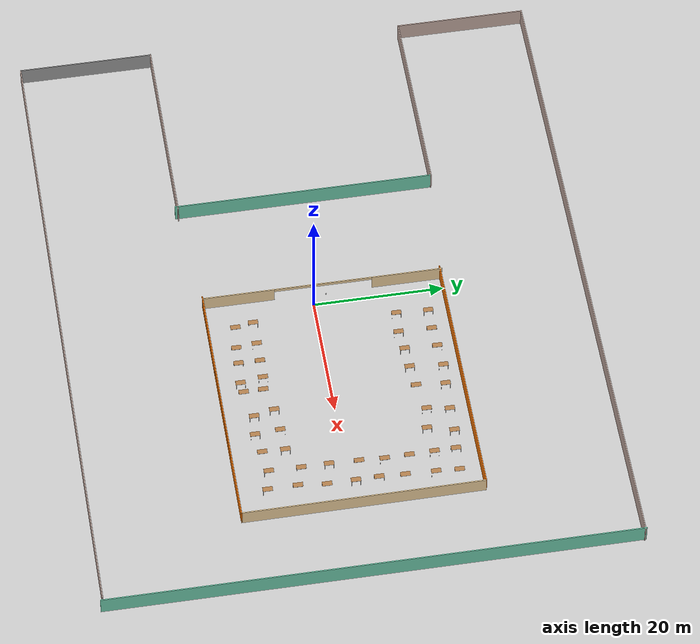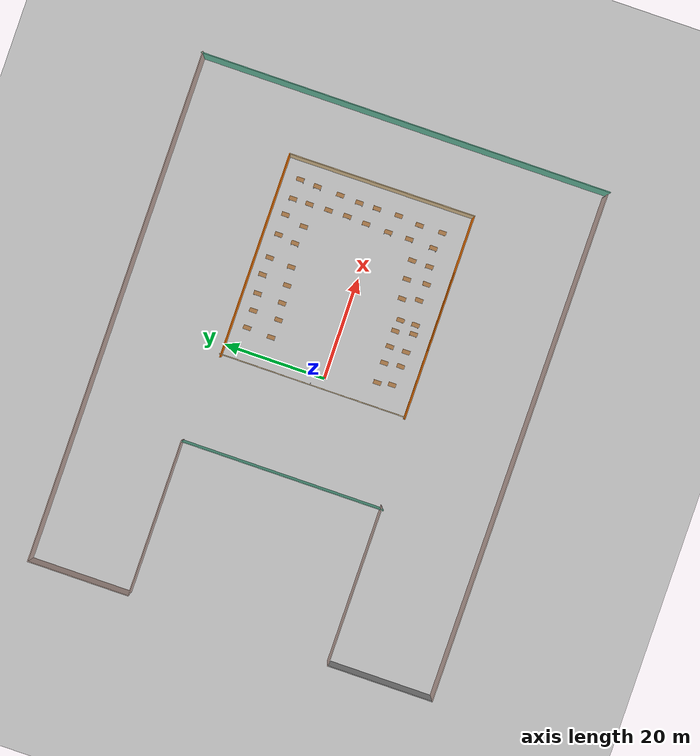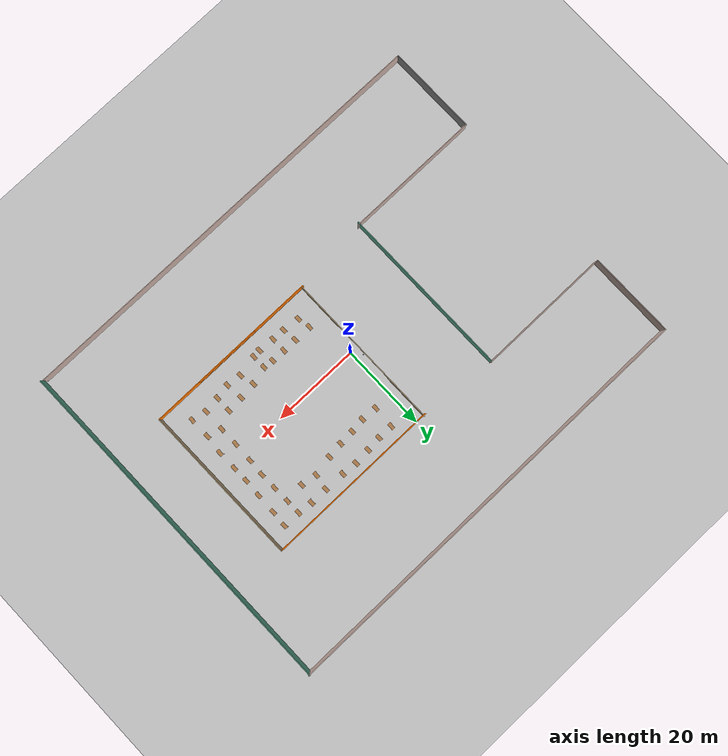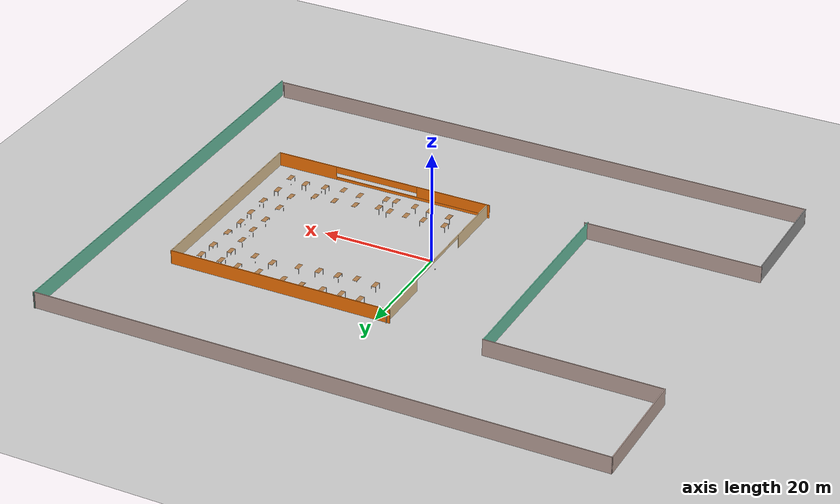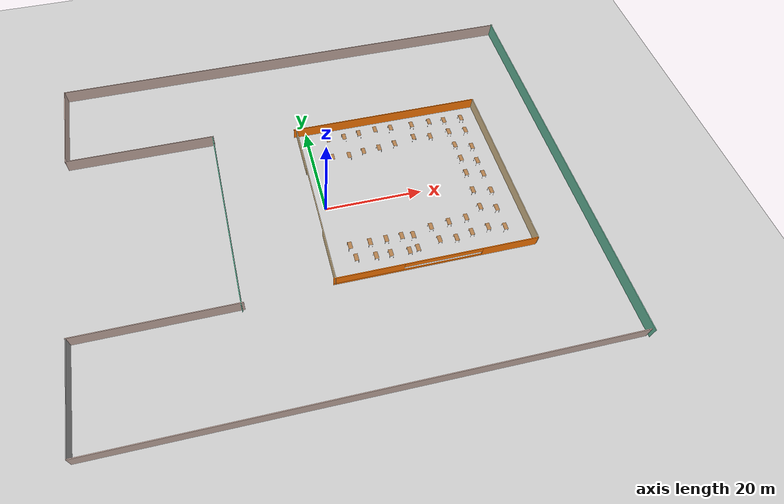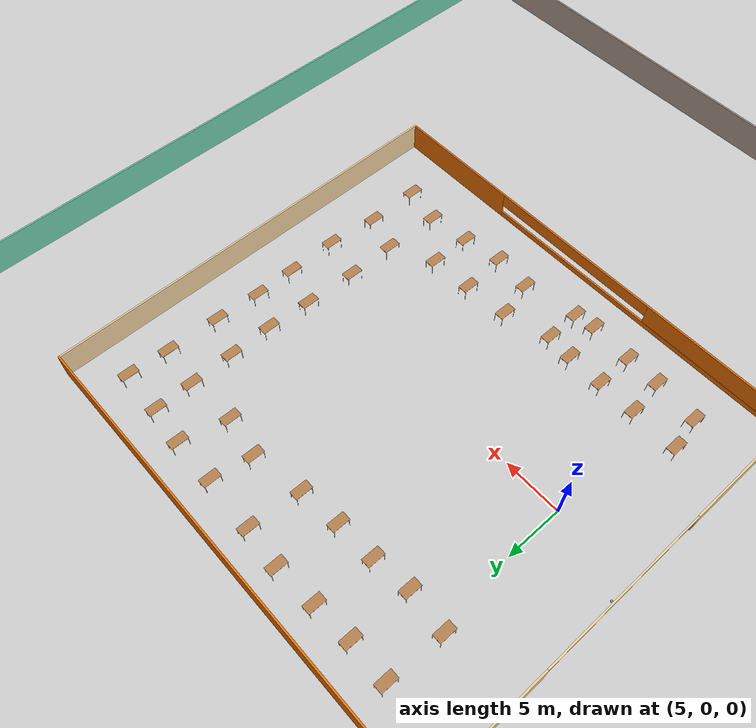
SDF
<sdf version="1.6">
 <world name="default">
  <plugin name="hello" filename="libhello.so"/>
  <light name="sun" type="directional">
   <pose>0 0 10 0 -0 0</pose>
   <diffuse>0.8 0.8 0.8 1</diffuse>
   <specular>0.2 0.2 0.2 1</specular>
   <attenuation>
    <range>1000</range>
    <constant>0.9</constant>
    <linear>0.01</linear>
    <quadratic>0.001</quadratic>
   </attenuation>
   <direction>-0.5 0.1 -0.9</direction>
  </light>
  <model name="ground_plane">
   <static>1</static>
   <link name="link">
    <collision name="collision">
     <geometry><plane><normal>0 0 1</normal><size>100 100</size></plane></geometry>
     <surface>
      <contact><collide_bitmask>65535</collide_bitmask></contact>
      <friction><ode><mu>100</mu><mu2>50</mu2></ode></friction>
     </surface>
    </collision>
    <visual name="visual">
     <cast_shadows>0</cast_shadows>
     <geometry><plane><normal>0 0 1</normal><size>100 100</size></plane></geometry>
     <material>
      <script><uri>file://media/materials/scripts/gazebo.material</uri><name>Gazebo/Grey</name></script>
     </material>
    </visual>
   </link>
  </model>
  <gravity>0 0 -9.8</gravity>
  <magnetic_field>6e-06 2.3e-05 -4.2e-05</magnetic_field>
  <atmosphere type="adiabatic"/>
  <physics name="default_physics" default="0" type="ode">
   <max_step_size>0.001</max_step_size>
   <real_time_factor>1</real_time_factor>
   <real_time_update_rate>1000</real_time_update_rate>
  </physics>
  <scene><ambient>0.4 0.4 0.4 1</ambient><background>0.7 0.7 0.7 1</background><shadows>1</shadows></scene>
  <spherical_coordinates>
   <surface_model>EARTH_WGS84</surface_model>
   <latitude_deg>0</latitude_deg>
   <longitude_deg>0</longitude_deg>
   <elevation>0</elevation>
   <heading_deg>0</heading_deg>
  </spherical_coordinates>
  <model name="building">
   <pose>-0.109009 1.0921 0 0 -0 0</pose>
   <link name="Wall_0">
    <collision name="Wall_0_Collision">
     <geometry><box><size>101 0.15 3</size></box></geometry>
     <pose>0 0 1.5 0 -0 0</pose>
    </collision>
    <visual name="Wall_0_Visual">
     <pose>0 0 1.5 0 -0 0</pose>
     <geometry><box><size>101 0.15 3</size></box></geometry>
     <material>
      <script><uri>file://media/materials/scripts/gazebo.material</uri><name>Gazebo/Grey</name></script>
      <ambient>0.760784 0.662745 0.627451 1</ambient>
     </material>
     <meta><layer>0</layer></meta>
    </visual>
    <pose>0.173498 40.2649 0 0 -0 0</pose>
   </link>
   <link name="Wall_10">
    <collision name="Wall_10_Collision">
     <geometry><box><size>31.5 0.15 3</size></box></geometry>
     <pose>0 0 1.5 0 -0 0</pose>
    </collision>
    <visual name="Wall_10_Visual">
     <pose>0 0 1.5 0 -0 0</pose>
     <geometry><box><size>31.5 0.15 3</size></box></geometry>
     <material>
      <script><uri>file://media/materials/scripts/gazebo.material</uri><name>Gazebo/Grey</name></script>
      <ambient>0.760784 0.662745 0.627451 1</ambient>
     </material>
     <meta><layer>0</layer></meta>
    </visual>
    <pose>-34.9235 -19.2011 0 0 -0 3.14159</pose>
   </link>
   <link name="Wall_13">
    <collision name="Wall_13_Collision">
     <geometry><box><size>0.16 0.15 2.5</size></box></geometry>
     <pose>0 0 1.25 0 -0 0</pose>
    </collision>
    <visual name="Wall_13_Visual">
     <pose>0 0 1.25 0 -0 0</pose>
     <geometry><box><size>0.16 0.15 2.5</size></box></geometry>
     <material>
      <script><uri>file://media/materials/scripts/gazebo.material</uri><name>Gazebo/Grey</name></script>
      <ambient>1 1 1 1</ambient>
     </material>
     <meta><layer>0</layer></meta>
    </visual>
    <pose>50.4165 40.425 0 0 -0 0</pose>
   </link>
   <link name="Wall_14">
    <collision name="Wall_14_Collision">
     <geometry><box><size>81 0.15 3</size></box></geometry>
     <pose>0 0 1.5 0 -0 0</pose>
    </collision>
    <visual name="Wall_14_Visual">
     <pose>0 0 1.5 0 -0 0</pose>
     <geometry><box><size>81 0.15 3</size></box></geometry>
     <material>
      <script><uri>file://media/materials/scripts/gazebo.material</uri><name>Gazebo/Grey</name></script>
      <ambient>0.435294 0.796078 0.67451 1</ambient>
     </material>
     <meta><layer>0</layer></meta>
    </visual>
    <pose>50.4215 0 0 0 0 -1.5708</pose>
   </link>
   <link name="Wall_16">
    <collision name="Wall_16_Collision">
     <geometry><box><size>0.16 0.15 2.5</size></box></geometry>
     <pose>0 0 1.25 0 -0 0</pose>
    </collision>
    <visual name="Wall_16_Visual">
     <pose>0 0 1.25 0 -0 0</pose>
     <geometry><box><size>0.16 0.15 2.5</size></box></geometry>
     <material>
      <script><uri>file://media/materials/scripts/gazebo.material</uri><name>Gazebo/Grey</name></script>
      <ambient>1 1 1 1</ambient>
     </material>
     <meta><layer>0</layer></meta>
    </visual>
    <pose>49.8404 -40.0869 0 0 0 -0.020117</pose>
   </link>
   <link name="Wall_17">
    <collision name="Wall_17_Collision">
     <geometry><box><size>100.5 0.15 3</size></box></geometry>
     <pose>0 0 1.5 0 -0 0</pose>
    </collision>
    <visual name="Wall_17_Visual">
     <pose>0 0 1.5 0 -0 0</pose>
     <geometry><box><size>100.5 0.15 3</size></box></geometry>
     <material>
      <script><uri>file://media/materials/scripts/gazebo.material</uri><name>Gazebo/Grey</name></script>
      <ambient>0.760784 0.662745 0.627451 1</ambient>
     </material>
     <meta><layer>0</layer></meta>
    </visual>
    <pose>-0.329256 -39.9628 0 0 -0 3.13912</pose>
   </link>
   <link name="Wall_18">
    <collision name="Wall_18_Collision">
     <geometry><box><size>20.75 0.15 3</size></box></geometry>
     <pose>0 0 1.5 0 -0 0</pose>
    </collision>
    <visual name="Wall_18_Visual">
     <pose>0 0 1.5 0 -0 0</pose>
     <geometry><box><size>20.75 0.15 3</size></box></geometry>
     <material>
      <script><uri>file://media/materials/scripts/gazebo.material</uri><name>Gazebo/Grey</name></script>
      <ambient>1 1 1 1</ambient>
     </material>
     <meta><layer>0</layer></meta>
    </visual>
    <pose>-50.504 -29.5385 0 0 -0 1.5708</pose>
   </link>
   <link name="Wall_2">
    <collision name="Wall_2_Collision">
     <geometry><box><size>20 0.15 3</size></box></geometry>
     <pose>0 0 1.5 0 -0 0</pose>
    </collision>
    <visual name="Wall_2_Visual">
     <pose>0 0 1.5 0 -0 0</pose>
     <geometry><box><size>20 0.15 3</size></box></geometry>
     <material>
      <script><uri>file://media/materials/scripts/gazebo.material</uri><name>Gazebo/Grey</name></script>
      <ambient>0.760784 0.662745 0.627451 1</ambient>
     </material>
     <meta><layer>0</layer></meta>
    </visual>
    <pose>-50.2515 30.3399 0 0 0 -1.5708</pose>
   </link>
   <link name="Wall_20">
    <collision name="Wall_20_Collision">
     <geometry><box><size>40.5 0.15 2.5</size></box></geometry>
     <pose>0 0 1.25 0 -0 0</pose>
    </collision>
    <visual name="Wall_20_Visual">
     <pose>0 0 1.25 0 -0 0</pose>
     <geometry><box><size>40.5 0.15 2.5</size></box></geometry>
     <material>
      <script><uri>file://media/materials/scripts/gazebo.material</uri><name>Gazebo/Grey</name></script>
      <ambient>0.996078 0.47451 0.0196078 1</ambient>
     </material>
     <meta><layer>0</layer></meta>
    </visual>
    <pose>17.8014 18.7619 0 0 -0 0</pose>
   </link>
   <link name="Wall_21">
    <collision name="Wall_21_Collision">
     <geometry><box><size>36.8158 0.15 2.5</size></box></geometry>
     <pose>0 0 1.25 0 -0 0</pose>
    </collision>
    <visual name="Wall_21_Visual">
     <pose>0 0 1.25 0 -0 0</pose>
     <geometry><box><size>36.8158 0.15 2.5</size></box></geometry>
     <material>
      <script><uri>file://media/materials/scripts/gazebo.material</uri><name>Gazebo/Grey</name></script>
      <ambient>0.921569 0.807843 0.615686 1</ambient>
     </material>
     <meta><layer>0</layer></meta>
    </visual>
    <pose>38.0513 0.429146 0 0 0 -1.56671</pose>
   </link>
   <link name="Wall_22">
    <pose>17.9513 -17.9036 0 0 -0 3.14159</pose>
    <visual name="Wall_22_Visual_0">
     <pose>-14.6255 0 1.25 0 -0 0</pose>
     <geometry><box><size>11.2491 0.15 2.5</size></box></geometry>
     <material>
      <script><uri>file://media/materials/scripts/gazebo.material</uri><name>Gazebo/Grey</name></script>
      <ambient>0.996078 0.47451 0.0196078 1</ambient>
     </material>
     <meta><layer>0</layer></meta>
    </visual>
    <collision name="Wall_22_Collision_0">
     <geometry><box><size>11.2491 0.15 2.5</size></box></geometry>
     <pose>-14.6255 0 1.25 0 -0 0</pose>
    </collision>
    <visual name="Wall_22_Visual_1">
     <pose>5.62455 0 0.25 0 -0 0</pose>
     <geometry><box><size>29.2509 0.15 0.5</size></box></geometry>
     <material>
      <script><uri>file://media/materials/scripts/gazebo.material</uri><name>Gazebo/Grey</name></script>
      <ambient>0.996078 0.47451 0.0196078 1</ambient>
     </material>
     <meta><layer>0</layer></meta>
    </visual>
    <collision name="Wall_22_Collision_1">
     <geometry><box><size>29.2509 0.15 0.5</size></box></geometry>
     <pose>5.62455 0 0.25 0 -0 0</pose>
    </collision>
    <visual name="Wall_22_Visual_2">
     <pose>13.3636 0 1.5 0 -0 0</pose>
     <geometry><box><size>13.7728 0.15 2</size></box></geometry>
     <material>
      <script><uri>file://media/materials/scripts/gazebo.material</uri><name>Gazebo/Grey</name></script>
      <ambient>0.996078 0.47451 0.0196078 1</ambient>
     </material>
     <meta><layer>0</layer></meta>
    </visual>
    <collision name="Wall_22_Collision_2">
     <geometry><box><size>13.7728 0.15 2</size></box></geometry>
     <pose>13.3636 0 1.5 0 -0 0</pose>
    </collision>
    <visual name="Wall_22_Visual_3">
     <pose>-1.26183 0 1.9 0 -0 0</pose>
     <geometry><box><size>15.4782 0.15 1.2</size></box></geometry>
     <material>
      <script><uri>file://media/materials/scripts/gazebo.material</uri><name>Gazebo/Grey</name></script>
      <ambient>0.996078 0.47451 0.0196078 1</ambient>
     </material>
     <meta><layer>0</layer></meta>
    </visual>
    <collision name="Wall_22_Collision_3">
     <geometry><box><size>15.4782 0.15 1.2</size></box></geometry>
     <pose>-1.26183 0 1.9 0 -0 0</pose>
    </collision>
   </link>
   <link name="Wall_23">
    <pose>-1.86869 0.531521 0 0 -0 1.5708</pose>
    <visual name="Wall_23_Visual_0">
     <pose>-12.9542 0 1.25 0 -0 0</pose>
     <geometry><box><size>11.1118 0.15 2.5</size></box></geometry>
     <material>
      <script><uri>file://media/materials/scripts/gazebo.material</uri><name>Gazebo/Grey</name></script>
      <ambient>0.921569 0.807843 0.615686 1</ambient>
     </material>
     <meta><layer>0</layer></meta>
    </visual>
    <collision name="Wall_23_Collision_0">
     <geometry><box><size>11.1118 0.15 2.5</size></box></geometry>
     <pose>-12.9542 0 1.25 0 -0 0</pose>
    </collision>
    <visual name="Wall_23_Visual_1">
     <pose>13.0636 0 1.25 0 -0 0</pose>
     <geometry><box><size>10.893 0.15 2.5</size></box></geometry>
     <material>
      <script><uri>file://media/materials/scripts/gazebo.material</uri><name>Gazebo/Grey</name></script>
      <ambient>0.921569 0.807843 0.615686 1</ambient>
     </material>
     <meta><layer>0</layer></meta>
    </visual>
    <collision name="Wall_23_Collision_1">
     <geometry><box><size>10.893 0.15 2.5</size></box></geometry>
     <pose>13.0636 0 1.25 0 -0 0</pose>
    </collision>
    <visual name="Wall_23_Visual_2">
     <pose>0.109402 0 2.25 0 -0 0</pose>
     <geometry><box><size>15.0155 0.15 0.5</size></box></geometry>
     <material>
      <script><uri>file://media/materials/scripts/gazebo.material</uri><name>Gazebo/Grey</name></script>
      <ambient>0.921569 0.807843 0.615686 1</ambient>
     </material>
     <meta><layer>0</layer></meta>
    </visual>
    <collision name="Wall_23_Collision_2">
     <geometry><box><size>15.0155 0.15 0.5</size></box></geometry>
     <pose>0.109402 0 2.25 0 -0 0</pose>
    </collision>
   </link>
   <link name="Wall_3">
    <collision name="Wall_3_Collision">
     <geometry><box><size>30.8 0.15 3</size></box></geometry>
     <pose>0 0 1.5 0 -0 0</pose>
    </collision>
    <visual name="Wall_3_Visual">
     <pose>0 0 1.5 0 -0 0</pose>
     <geometry><box><size>30.8 0.15 3</size></box></geometry>
     <material>
      <script><uri>file://media/materials/scripts/gazebo.material</uri><name>Gazebo/Grey</name></script>
      <ambient>0.760784 0.662745 0.627451 1</ambient>
     </material>
     <meta><layer>0</layer></meta>
    </visual>
    <pose>-34.9265 20.4149 0 0 -0 0</pose>
   </link>
   <link name="Wall_8">
    <collision name="Wall_8_Collision">
     <geometry><box><size>40 0.15 3</size></box></geometry>
     <pose>0 0 1.5 0 -0 0</pose>
    </collision>
    <visual name="Wall_8_Visual">
     <pose>0 0 1.5 0 -0 0</pose>
     <geometry><box><size>40 0.15 3</size></box></geometry>
     <material>
      <script><uri>file://media/materials/scripts/gazebo.material</uri><name>Gazebo/Grey</name></script>
      <ambient>0.435294 0.796078 0.67451 1</ambient>
     </material>
     <meta><layer>0</layer></meta>
    </visual>
    <pose>-19.7001 0.327961 0 0 0 -1.5708</pose>
   </link>
   <static>1</static>
  </model>
  <model name="table">
   <static>1</static>
   <link name="link">
    <collision name="surface">
     <pose>0 0 1 0 -0 0</pose>
     <geometry><box><size>1.5 0.8 0.03</size></box></geometry>
     <surface><friction><ode><mu>0.6</mu><mu2>0.6</mu2></ode></friction></surface>
    </collision>
    <visual name="visual1">
     <pose>0 0 1 0 -0 0</pose>
     <geometry><box><size>1.5 0.8 0.03</size></box></geometry>
     <material>
      <script><uri>file://media/materials/scripts/gazebo.material</uri><name>Gazebo/Wood</name></script>
     </material>
    </visual>
    <collision name="front_left_leg">
     <pose>0.68 0.38 0.5 0 -0 0</pose>
     <geometry><cylinder><radius>0.02</radius><length>1</length></cylinder></geometry>
    </collision>
    <visual name="front_left_leg">
     <pose>0.68 0.38 0.5 0 -0 0</pose>
     <geometry><cylinder><radius>0.02</radius><length>1</length></cylinder></geometry>
     <material>
      <script><uri>file://media/materials/scripts/gazebo.material</uri><name>Gazebo/Grey</name></script>
     </material>
    </visual>
    <collision name="front_right_leg">
     <pose>0.68 -0.38 0.5 0 -0 0</pose>
     <geometry><cylinder><radius>0.02</radius><length>1</length></cylinder></geometry>
    </collision>
    <visual name="front_right_leg">
     <pose>0.68 -0.38 0.5 0 -0 0</pose>
     <geometry><cylinder><radius>0.02</radius><length>1</length></cylinder></geometry>
     <material>
      <script><uri>file://media/materials/scripts/gazebo.material</uri><name>Gazebo/Grey</name></script>
     </material>
    </visual>
    <collision name="back_right_leg">
     <pose>-0.68 -0.38 0.5 0 -0 0</pose>
     <geometry><cylinder><radius>0.02</radius><length>1</length></cylinder></geometry>
    </collision>
    <visual name="back_right_leg">
     <pose>-0.68 -0.38 0.5 0 -0 0</pose>
     <geometry><cylinder><radius>0.02</radius><length>1</length></cylinder></geometry>
     <material>
      <script><uri>file://media/materials/scripts/gazebo.material</uri><name>Gazebo/Grey</name></script>
     </material>
    </visual>
    <collision name="back_left_leg">
     <pose>-0.68 0.38 0.5 0 -0 0</pose>
     <geometry><cylinder><radius>0.02</radius><length>1</length></cylinder></geometry>
    </collision>
    <visual name="back_left_leg">
     <pose>-0.68 0.38 0.5 0 -0 0</pose>
     <geometry><cylinder><radius>0.02</radius><length>1</length></cylinder></geometry>
     <material>
      <script><uri>file://media/materials/scripts/gazebo.material</uri><name>Gazebo/Grey</name></script>
     </material>
    </visual>
   </link>
   <pose>2.54233 -9.76678 0 0 0 -1.57678</pose>
  </model>
  <model name="table_clone">
   <static>1</static>
   <link name="link">
    <collision name="surface">
     <pose>0 0 1 0 -0 0</pose>
     <geometry><box><size>1.5 0.8 0.03</size></box></geometry>
     <surface><friction><ode><mu>0.6</mu><mu2>0.6</mu2></ode></friction></surface>
    </collision>
    <visual name="visual1">
     <pose>0 0 1 0 -0 0</pose>
     <geometry><box><size>1.5 0.8 0.03</size></box></geometry>
     <material>
      <script><uri>file://media/materials/scripts/gazebo.material</uri><name>Gazebo/Wood</name></script>
     </material>
    </visual>
    <collision name="front_left_leg">
     <pose>0.68 0.38 0.5 0 -0 0</pose>
     <geometry><cylinder><radius>0.02</radius><length>1</length></cylinder></geometry>
    </collision>
    <visual name="front_left_leg">
     <pose>0.68 0.38 0.5 0 -0 0</pose>
     <geometry><cylinder><radius>0.02</radius><length>1</length></cylinder></geometry>
     <material>
      <script><uri>file://media/materials/scripts/gazebo.material</uri><name>Gazebo/Grey</name></script>
     </material>
    </visual>
    <collision name="front_right_leg">
     <pose>0.68 -0.38 0.5 0 -0 0</pose>
     <geometry><cylinder><radius>0.02</radius><length>1</length></cylinder></geometry>
    </collision>
    <visual name="front_right_leg">
     <pose>0.68 -0.38 0.5 0 -0 0</pose>
     <geometry><cylinder><radius>0.02</radius><length>1</length></cylinder></geometry>
     <material>
      <script><uri>file://media/materials/scripts/gazebo.material</uri><name>Gazebo/Grey</name></script>
     </material>
    </visual>
    <collision name="back_right_leg">
     <pose>-0.68 -0.38 0.5 0 -0 0</pose>
     <geometry><cylinder><radius>0.02</radius><length>1</length></cylinder></geometry>
    </collision>
    <visual name="back_right_leg">
     <pose>-0.68 -0.38 0.5 0 -0 0</pose>
     <geometry><cylinder><radius>0.02</radius><length>1</length></cylinder></geometry>
     <material>
      <script><uri>file://media/materials/scripts/gazebo.material</uri><name>Gazebo/Grey</name></script>
     </material>
    </visual>
    <collision name="back_left_leg">
     <pose>-0.68 0.38 0.5 0 -0 0</pose>
     <geometry><cylinder><radius>0.02</radius><length>1</length></cylinder></geometry>
    </collision>
    <visual name="back_left_leg">
     <pose>-0.68 0.38 0.5 0 -0 0</pose>
     <geometry><cylinder><radius>0.02</radius><length>1</length></cylinder></geometry>
     <material>
      <script><uri>file://media/materials/scripts/gazebo.material</uri><name>Gazebo/Grey</name></script>
     </material>
    </visual>
   </link>
   <pose>6.50563 -9.80936 0 0 0 -1.57678</pose>
  </model>
  <model name="table_clone_0">
   <static>1</static>
   <link name="link">
    <collision name="surface">
     <pose>0 0 1 0 -0 0</pose>
     <geometry><box><size>1.5 0.8 0.03</size></box></geometry>
     <surface><friction><ode><mu>0.6</mu><mu2>0.6</mu2></ode></friction></surface>
    </collision>
    <visual name="visual1">
     <pose>0 0 1 0 -0 0</pose>
     <geometry><box><size>1.5 0.8 0.03</size></box></geometry>
     <material>
      <script><uri>file://media/materials/scripts/gazebo.material</uri><name>Gazebo/Wood</name></script>
     </material>
    </visual>
    <collision name="front_left_leg">
     <pose>0.68 0.38 0.5 0 -0 0</pose>
     <geometry><cylinder><radius>0.02</radius><length>1</length></cylinder></geometry>
    </collision>
    <visual name="front_left_leg">
     <pose>0.68 0.38 0.5 0 -0 0</pose>
     <geometry><cylinder><radius>0.02</radius><length>1</length></cylinder></geometry>
     <material>
      <script><uri>file://media/materials/scripts/gazebo.material</uri><name>Gazebo/Grey</name></script>
     </material>
    </visual>
    <collision name="front_right_leg">
     <pose>0.68 -0.38 0.5 0 -0 0</pose>
     <geometry><cylinder><radius>0.02</radius><length>1</length></cylinder></geometry>
    </collision>
    <visual name="front_right_leg">
     <pose>0.68 -0.38 0.5 0 -0 0</pose>
     <geometry><cylinder><radius>0.02</radius><length>1</length></cylinder></geometry>
     <material>
      <script><uri>file://media/materials/scripts/gazebo.material</uri><name>Gazebo/Grey</name></script>
     </material>
    </visual>
    <collision name="back_right_leg">
     <pose>-0.68 -0.38 0.5 0 -0 0</pose>
     <geometry><cylinder><radius>0.02</radius><length>1</length></cylinder></geometry>
    </collision>
    <visual name="back_right_leg">
     <pose>-0.68 -0.38 0.5 0 -0 0</pose>
     <geometry><cylinder><radius>0.02</radius><length>1</length></cylinder></geometry>
     <material>
      <script><uri>file://media/materials/scripts/gazebo.material</uri><name>Gazebo/Grey</name></script>
     </material>
    </visual>
    <collision name="back_left_leg">
     <pose>-0.68 0.38 0.5 0 -0 0</pose>
     <geometry><cylinder><radius>0.02</radius><length>1</length></cylinder></geometry>
    </collision>
    <visual name="back_left_leg">
     <pose>-0.68 0.38 0.5 0 -0 0</pose>
     <geometry><cylinder><radius>0.02</radius><length>1</length></cylinder></geometry>
     <material>
      <script><uri>file://media/materials/scripts/gazebo.material</uri><name>Gazebo/Grey</name></script>
     </material>
    </visual>
   </link>
   <pose>9.76275 -9.80948 0 0 0 -1.57678</pose>
  </model>
  <model name="table_clone_1">
   <static>1</static>
   <link name="link">
    <collision name="surface">
     <pose>0 0 1 0 -0 0</pose>
     <geometry><box><size>1.5 0.8 0.03</size></box></geometry>
     <surface><friction><ode><mu>0.6</mu><mu2>0.6</mu2></ode></friction></surface>
    </collision>
    <visual name="visual1">
     <pose>0 0 1 0 -0 0</pose>
     <geometry><box><size>1.5 0.8 0.03</size></box></geometry>
     <material>
      <script><uri>file://media/materials/scripts/gazebo.material</uri><name>Gazebo/Wood</name></script>
     </material>
    </visual>
    <collision name="front_left_leg">
     <pose>0.68 0.38 0.5 0 -0 0</pose>
     <geometry><cylinder><radius>0.02</radius><length>1</length></cylinder></geometry>
    </collision>
    <visual name="front_left_leg">
     <pose>0.68 0.38 0.5 0 -0 0</pose>
     <geometry><cylinder><radius>0.02</radius><length>1</length></cylinder></geometry>
     <material>
      <script><uri>file://media/materials/scripts/gazebo.material</uri><name>Gazebo/Grey</name></script>
     </material>
    </visual>
    <collision name="front_right_leg">
     <pose>0.68 -0.38 0.5 0 -0 0</pose>
     <geometry><cylinder><radius>0.02</radius><length>1</length></cylinder></geometry>
    </collision>
    <visual name="front_right_leg">
     <pose>0.68 -0.38 0.5 0 -0 0</pose>
     <geometry><cylinder><radius>0.02</radius><length>1</length></cylinder></geometry>
     <material>
      <script><uri>file://media/materials/scripts/gazebo.material</uri><name>Gazebo/Grey</name></script>
     </material>
    </visual>
    <collision name="back_right_leg">
     <pose>-0.68 -0.38 0.5 0 -0 0</pose>
     <geometry><cylinder><radius>0.02</radius><length>1</length></cylinder></geometry>
    </collision>
    <visual name="back_right_leg">
     <pose>-0.68 -0.38 0.5 0 -0 0</pose>
     <geometry><cylinder><radius>0.02</radius><length>1</length></cylinder></geometry>
     <material>
      <script><uri>file://media/materials/scripts/gazebo.material</uri><name>Gazebo/Grey</name></script>
     </material>
    </visual>
    <collision name="back_left_leg">
     <pose>-0.68 0.38 0.5 0 -0 0</pose>
     <geometry><cylinder><radius>0.02</radius><length>1</length></cylinder></geometry>
    </collision>
    <visual name="back_left_leg">
     <pose>-0.68 0.38 0.5 0 -0 0</pose>
     <geometry><cylinder><radius>0.02</radius><length>1</length></cylinder></geometry>
     <material>
      <script><uri>file://media/materials/scripts/gazebo.material</uri><name>Gazebo/Grey</name></script>
     </material>
    </visual>
   </link>
   <pose>12.8871 -9.82897 0 0 0 -1.57678</pose>
  </model>
  <model name="table_clone_2">
   <static>1</static>
   <link name="link">
    <collision name="surface">
     <pose>0 0 1 0 -0 0</pose>
     <geometry><box><size>1.5 0.8 0.03</size></box></geometry>
     <surface><friction><ode><mu>0.6</mu><mu2>0.6</mu2></ode></friction></surface>
    </collision>
    <visual name="visual1">
     <pose>0 0 1 0 -0 0</pose>
     <geometry><box><size>1.5 0.8 0.03</size></box></geometry>
     <material>
      <script><uri>file://media/materials/scripts/gazebo.material</uri><name>Gazebo/Wood</name></script>
     </material>
    </visual>
    <collision name="front_left_leg">
     <pose>0.68 0.38 0.5 0 -0 0</pose>
     <geometry><cylinder><radius>0.02</radius><length>1</length></cylinder></geometry>
    </collision>
    <visual name="front_left_leg">
     <pose>0.68 0.38 0.5 0 -0 0</pose>
     <geometry><cylinder><radius>0.02</radius><length>1</length></cylinder></geometry>
     <material>
      <script><uri>file://media/materials/scripts/gazebo.material</uri><name>Gazebo/Grey</name></script>
     </material>
    </visual>
    <collision name="front_right_leg">
     <pose>0.68 -0.38 0.5 0 -0 0</pose>
     <geometry><cylinder><radius>0.02</radius><length>1</length></cylinder></geometry>
    </collision>
    <visual name="front_right_leg">
     <pose>0.68 -0.38 0.5 0 -0 0</pose>
     <geometry><cylinder><radius>0.02</radius><length>1</length></cylinder></geometry>
     <material>
      <script><uri>file://media/materials/scripts/gazebo.material</uri><name>Gazebo/Grey</name></script>
     </material>
    </visual>
    <collision name="back_right_leg">
     <pose>-0.68 -0.38 0.5 0 -0 0</pose>
     <geometry><cylinder><radius>0.02</radius><length>1</length></cylinder></geometry>
    </collision>
    <visual name="back_right_leg">
     <pose>-0.68 -0.38 0.5 0 -0 0</pose>
     <geometry><cylinder><radius>0.02</radius><length>1</length></cylinder></geometry>
     <material>
      <script><uri>file://media/materials/scripts/gazebo.material</uri><name>Gazebo/Grey</name></script>
     </material>
    </visual>
    <collision name="back_left_leg">
     <pose>-0.68 0.38 0.5 0 -0 0</pose>
     <geometry><cylinder><radius>0.02</radius><length>1</length></cylinder></geometry>
    </collision>
    <visual name="back_left_leg">
     <pose>-0.68 0.38 0.5 0 -0 0</pose>
     <geometry><cylinder><radius>0.02</radius><length>1</length></cylinder></geometry>
     <material>
      <script><uri>file://media/materials/scripts/gazebo.material</uri><name>Gazebo/Grey</name></script>
     </material>
    </visual>
   </link>
   <pose>6.8781 -12.9747 0 0 0 -1.57678</pose>
  </model>
  <model name="table_clone_3">
   <static>1</static>
   <link name="link">
    <collision name="surface">
     <pose>0 0 1 0 -0 0</pose>
     <geometry><box><size>1.5 0.8 0.03</size></box></geometry>
     <surface><friction><ode><mu>0.6</mu><mu2>0.6</mu2></ode></friction></surface>
    </collision>
    <visual name="visual1">
     <pose>0 0 1 0 -0 0</pose>
     <geometry><box><size>1.5 0.8 0.03</size></box></geometry>
     <material>
      <script><uri>file://media/materials/scripts/gazebo.material</uri><name>Gazebo/Wood</name></script>
     </material>
    </visual>
    <collision name="front_left_leg">
     <pose>0.68 0.38 0.5 0 -0 0</pose>
     <geometry><cylinder><radius>0.02</radius><length>1</length></cylinder></geometry>
    </collision>
    <visual name="front_left_leg">
     <pose>0.68 0.38 0.5 0 -0 0</pose>
     <geometry><cylinder><radius>0.02</radius><length>1</length></cylinder></geometry>
     <material>
      <script><uri>file://media/materials/scripts/gazebo.material</uri><name>Gazebo/Grey</name></script>
     </material>
    </visual>
    <collision name="front_right_leg">
     <pose>0.68 -0.38 0.5 0 -0 0</pose>
     <geometry><cylinder><radius>0.02</radius><length>1</length></cylinder></geometry>
    </collision>
    <visual name="front_right_leg">
     <pose>0.68 -0.38 0.5 0 -0 0</pose>
     <geometry><cylinder><radius>0.02</radius><length>1</length></cylinder></geometry>
     <material>
      <script><uri>file://media/materials/scripts/gazebo.material</uri><name>Gazebo/Grey</name></script>
     </material>
    </visual>
    <collision name="back_right_leg">
     <pose>-0.68 -0.38 0.5 0 -0 0</pose>
     <geometry><cylinder><radius>0.02</radius><length>1</length></cylinder></geometry>
    </collision>
    <visual name="back_right_leg">
     <pose>-0.68 -0.38 0.5 0 -0 0</pose>
     <geometry><cylinder><radius>0.02</radius><length>1</length></cylinder></geometry>
     <material>
      <script><uri>file://media/materials/scripts/gazebo.material</uri><name>Gazebo/Grey</name></script>
     </material>
    </visual>
    <collision name="back_left_leg">
     <pose>-0.68 0.38 0.5 0 -0 0</pose>
     <geometry><cylinder><radius>0.02</radius><length>1</length></cylinder></geometry>
    </collision>
    <visual name="back_left_leg">
     <pose>-0.68 0.38 0.5 0 -0 0</pose>
     <geometry><cylinder><radius>0.02</radius><length>1</length></cylinder></geometry>
     <material>
      <script><uri>file://media/materials/scripts/gazebo.material</uri><name>Gazebo/Grey</name></script>
     </material>
    </visual>
   </link>
   <pose>9.77098 -13.0717 0 0 0 -1.57678</pose>
  </model>
  <model name="table_clone_4">
   <static>1</static>
   <link name="link">
    <collision name="surface">
     <pose>0 0 1 0 -0 0</pose>
     <geometry><box><size>1.5 0.8 0.03</size></box></geometry>
     <surface><friction><ode><mu>0.6</mu><mu2>0.6</mu2></ode></friction></surface>
    </collision>
    <visual name="visual1">
     <pose>0 0 1 0 -0 0</pose>
     <geometry><box><size>1.5 0.8 0.03</size></box></geometry>
     <material>
      <script><uri>file://media/materials/scripts/gazebo.material</uri><name>Gazebo/Wood</name></script>
     </material>
    </visual>
    <collision name="front_left_leg">
     <pose>0.68 0.38 0.5 0 -0 0</pose>
     <geometry><cylinder><radius>0.02</radius><length>1</length></cylinder></geometry>
    </collision>
    <visual name="front_left_leg">
     <pose>0.68 0.38 0.5 0 -0 0</pose>
     <geometry><cylinder><radius>0.02</radius><length>1</length></cylinder></geometry>
     <material>
      <script><uri>file://media/materials/scripts/gazebo.material</uri><name>Gazebo/Grey</name></script>
     </material>
    </visual>
    <collision name="front_right_leg">
     <pose>0.68 -0.38 0.5 0 -0 0</pose>
     <geometry><cylinder><radius>0.02</radius><length>1</length></cylinder></geometry>
    </collision>
    <visual name="front_right_leg">
     <pose>0.68 -0.38 0.5 0 -0 0</pose>
     <geometry><cylinder><radius>0.02</radius><length>1</length></cylinder></geometry>
     <material>
      <script><uri>file://media/materials/scripts/gazebo.material</uri><name>Gazebo/Grey</name></script>
     </material>
    </visual>
    <collision name="back_right_leg">
     <pose>-0.68 -0.38 0.5 0 -0 0</pose>
     <geometry><cylinder><radius>0.02</radius><length>1</length></cylinder></geometry>
    </collision>
    <visual name="back_right_leg">
     <pose>-0.68 -0.38 0.5 0 -0 0</pose>
     <geometry><cylinder><radius>0.02</radius><length>1</length></cylinder></geometry>
     <material>
      <script><uri>file://media/materials/scripts/gazebo.material</uri><name>Gazebo/Grey</name></script>
     </material>
    </visual>
    <collision name="back_left_leg">
     <pose>-0.68 0.38 0.5 0 -0 0</pose>
     <geometry><cylinder><radius>0.02</radius><length>1</length></cylinder></geometry>
    </collision>
    <visual name="back_left_leg">
     <pose>-0.68 0.38 0.5 0 -0 0</pose>
     <geometry><cylinder><radius>0.02</radius><length>1</length></cylinder></geometry>
     <material>
      <script><uri>file://media/materials/scripts/gazebo.material</uri><name>Gazebo/Grey</name></script>
     </material>
    </visual>
   </link>
   <pose>13.4499 -13.3204 0 0 0 -1.57678</pose>
  </model>
  <model name="table_clone_5">
   <static>1</static>
   <link name="link">
    <collision name="surface">
     <pose>0 0 1 0 -0 0</pose>
     <geometry><box><size>1.5 0.8 0.03</size></box></geometry>
     <surface><friction><ode><mu>0.6</mu><mu2>0.6</mu2></ode></friction></surface>
    </collision>
    <visual name="visual1">
     <pose>0 0 1 0 -0 0</pose>
     <geometry><box><size>1.5 0.8 0.03</size></box></geometry>
     <material>
      <script><uri>file://media/materials/scripts/gazebo.material</uri><name>Gazebo/Wood</name></script>
     </material>
    </visual>
    <collision name="front_left_leg">
     <pose>0.68 0.38 0.5 0 -0 0</pose>
     <geometry><cylinder><radius>0.02</radius><length>1</length></cylinder></geometry>
    </collision>
    <visual name="front_left_leg">
     <pose>0.68 0.38 0.5 0 -0 0</pose>
     <geometry><cylinder><radius>0.02</radius><length>1</length></cylinder></geometry>
     <material>
      <script><uri>file://media/materials/scripts/gazebo.material</uri><name>Gazebo/Grey</name></script>
     </material>
    </visual>
    <collision name="front_right_leg">
     <pose>0.68 -0.38 0.5 0 -0 0</pose>
     <geometry><cylinder><radius>0.02</radius><length>1</length></cylinder></geometry>
    </collision>
    <visual name="front_right_leg">
     <pose>0.68 -0.38 0.5 0 -0 0</pose>
     <geometry><cylinder><radius>0.02</radius><length>1</length></cylinder></geometry>
     <material>
      <script><uri>file://media/materials/scripts/gazebo.material</uri><name>Gazebo/Grey</name></script>
     </material>
    </visual>
    <collision name="back_right_leg">
     <pose>-0.68 -0.38 0.5 0 -0 0</pose>
     <geometry><cylinder><radius>0.02</radius><length>1</length></cylinder></geometry>
    </collision>
    <visual name="back_right_leg">
     <pose>-0.68 -0.38 0.5 0 -0 0</pose>
     <geometry><cylinder><radius>0.02</radius><length>1</length></cylinder></geometry>
     <material>
      <script><uri>file://media/materials/scripts/gazebo.material</uri><name>Gazebo/Grey</name></script>
     </material>
    </visual>
    <collision name="back_left_leg">
     <pose>-0.68 0.38 0.5 0 -0 0</pose>
     <geometry><cylinder><radius>0.02</radius><length>1</length></cylinder></geometry>
    </collision>
    <visual name="back_left_leg">
     <pose>-0.68 0.38 0.5 0 -0 0</pose>
     <geometry><cylinder><radius>0.02</radius><length>1</length></cylinder></geometry>
     <material>
      <script><uri>file://media/materials/scripts/gazebo.material</uri><name>Gazebo/Grey</name></script>
     </material>
    </visual>
   </link>
   <pose>3.04773 -12.563 0 0 0 -1.57678</pose>
  </model>
  <model name="table_clone_6">
   <static>1</static>
   <link name="link">
    <collision name="surface">
     <pose>0 0 1 0 -0 0</pose>
     <geometry><box><size>1.5 0.8 0.03</size></box></geometry>
     <surface><friction><ode><mu>0.6</mu><mu2>0.6</mu2></ode></friction></surface>
    </collision>
    <visual name="visual1">
     <pose>0 0 1 0 -0 0</pose>
     <geometry><box><size>1.5 0.8 0.03</size></box></geometry>
     <material>
      <script><uri>file://media/materials/scripts/gazebo.material</uri><name>Gazebo/Wood</name></script>
     </material>
    </visual>
    <collision name="front_left_leg">
     <pose>0.68 0.38 0.5 0 -0 0</pose>
     <geometry><cylinder><radius>0.02</radius><length>1</length></cylinder></geometry>
    </collision>
    <visual name="front_left_leg">
     <pose>0.68 0.38 0.5 0 -0 0</pose>
     <geometry><cylinder><radius>0.02</radius><length>1</length></cylinder></geometry>
     <material>
      <script><uri>file://media/materials/scripts/gazebo.material</uri><name>Gazebo/Grey</name></script>
     </material>
    </visual>
    <collision name="front_right_leg">
     <pose>0.68 -0.38 0.5 0 -0 0</pose>
     <geometry><cylinder><radius>0.02</radius><length>1</length></cylinder></geometry>
    </collision>
    <visual name="front_right_leg">
     <pose>0.68 -0.38 0.5 0 -0 0</pose>
     <geometry><cylinder><radius>0.02</radius><length>1</length></cylinder></geometry>
     <material>
      <script><uri>file://media/materials/scripts/gazebo.material</uri><name>Gazebo/Grey</name></script>
     </material>
    </visual>
    <collision name="back_right_leg">
     <pose>-0.68 -0.38 0.5 0 -0 0</pose>
     <geometry><cylinder><radius>0.02</radius><length>1</length></cylinder></geometry>
    </collision>
    <visual name="back_right_leg">
     <pose>-0.68 -0.38 0.5 0 -0 0</pose>
     <geometry><cylinder><radius>0.02</radius><length>1</length></cylinder></geometry>
     <material>
      <script><uri>file://media/materials/scripts/gazebo.material</uri><name>Gazebo/Grey</name></script>
     </material>
    </visual>
    <collision name="back_left_leg">
     <pose>-0.68 0.38 0.5 0 -0 0</pose>
     <geometry><cylinder><radius>0.02</radius><length>1</length></cylinder></geometry>
    </collision>
    <visual name="back_left_leg">
     <pose>-0.68 0.38 0.5 0 -0 0</pose>
     <geometry><cylinder><radius>0.02</radius><length>1</length></cylinder></geometry>
     <material>
      <script><uri>file://media/materials/scripts/gazebo.material</uri><name>Gazebo/Grey</name></script>
     </material>
    </visual>
   </link>
   <pose>15.1994 -13.1014 0 0 0 -1.57678</pose>
  </model>
  <model name="table_clone_7">
   <static>1</static>
   <link name="link">
    <collision name="surface">
     <pose>0 0 1 0 -0 0</pose>
     <geometry><box><size>1.5 0.8 0.03</size></box></geometry>
     <surface><friction><ode><mu>0.6</mu><mu2>0.6</mu2></ode></friction></surface>
    </collision>
    <visual name="visual1">
     <pose>0 0 1 0 -0 0</pose>
     <geometry><box><size>1.5 0.8 0.03</size></box></geometry>
     <material>
      <script><uri>file://media/materials/scripts/gazebo.material</uri><name>Gazebo/Wood</name></script>
     </material>
    </visual>
    <collision name="front_left_leg">
     <pose>0.68 0.38 0.5 0 -0 0</pose>
     <geometry><cylinder><radius>0.02</radius><length>1</length></cylinder></geometry>
    </collision>
    <visual name="front_left_leg">
     <pose>0.68 0.38 0.5 0 -0 0</pose>
     <geometry><cylinder><radius>0.02</radius><length>1</length></cylinder></geometry>
     <material>
      <script><uri>file://media/materials/scripts/gazebo.material</uri><name>Gazebo/Grey</name></script>
     </material>
    </visual>
    <collision name="front_right_leg">
     <pose>0.68 -0.38 0.5 0 -0 0</pose>
     <geometry><cylinder><radius>0.02</radius><length>1</length></cylinder></geometry>
    </collision>
    <visual name="front_right_leg">
     <pose>0.68 -0.38 0.5 0 -0 0</pose>
     <geometry><cylinder><radius>0.02</radius><length>1</length></cylinder></geometry>
     <material>
      <script><uri>file://media/materials/scripts/gazebo.material</uri><name>Gazebo/Grey</name></script>
     </material>
    </visual>
    <collision name="back_right_leg">
     <pose>-0.68 -0.38 0.5 0 -0 0</pose>
     <geometry><cylinder><radius>0.02</radius><length>1</length></cylinder></geometry>
    </collision>
    <visual name="back_right_leg">
     <pose>-0.68 -0.38 0.5 0 -0 0</pose>
     <geometry><cylinder><radius>0.02</radius><length>1</length></cylinder></geometry>
     <material>
      <script><uri>file://media/materials/scripts/gazebo.material</uri><name>Gazebo/Grey</name></script>
     </material>
    </visual>
    <collision name="back_left_leg">
     <pose>-0.68 0.38 0.5 0 -0 0</pose>
     <geometry><cylinder><radius>0.02</radius><length>1</length></cylinder></geometry>
    </collision>
    <visual name="back_left_leg">
     <pose>-0.68 0.38 0.5 0 -0 0</pose>
     <geometry><cylinder><radius>0.02</radius><length>1</length></cylinder></geometry>
     <material>
      <script><uri>file://media/materials/scripts/gazebo.material</uri><name>Gazebo/Grey</name></script>
     </material>
    </visual>
   </link>
   <pose>15.1439 -10.1159 0 0 0 -1.57678</pose>
  </model>
  <model name="table_clone_8">
   <static>1</static>
   <link name="link">
    <collision name="surface">
     <pose>0 0 1 0 -0 0</pose>
     <geometry><box><size>1.5 0.8 0.03</size></box></geometry>
     <surface><friction><ode><mu>0.6</mu><mu2>0.6</mu2></ode></friction></surface>
    </collision>
    <visual name="visual1">
     <pose>0 0 1 0 -0 0</pose>
     <geometry><box><size>1.5 0.8 0.03</size></box></geometry>
     <material>
      <script><uri>file://media/materials/scripts/gazebo.material</uri><name>Gazebo/Wood</name></script>
     </material>
    </visual>
    <collision name="front_left_leg">
     <pose>0.68 0.38 0.5 0 -0 0</pose>
     <geometry><cylinder><radius>0.02</radius><length>1</length></cylinder></geometry>
    </collision>
    <visual name="front_left_leg">
     <pose>0.68 0.38 0.5 0 -0 0</pose>
     <geometry><cylinder><radius>0.02</radius><length>1</length></cylinder></geometry>
     <material>
      <script><uri>file://media/materials/scripts/gazebo.material</uri><name>Gazebo/Grey</name></script>
     </material>
    </visual>
    <collision name="front_right_leg">
     <pose>0.68 -0.38 0.5 0 -0 0</pose>
     <geometry><cylinder><radius>0.02</radius><length>1</length></cylinder></geometry>
    </collision>
    <visual name="front_right_leg">
     <pose>0.68 -0.38 0.5 0 -0 0</pose>
     <geometry><cylinder><radius>0.02</radius><length>1</length></cylinder></geometry>
     <material>
      <script><uri>file://media/materials/scripts/gazebo.material</uri><name>Gazebo/Grey</name></script>
     </material>
    </visual>
    <collision name="back_right_leg">
     <pose>-0.68 -0.38 0.5 0 -0 0</pose>
     <geometry><cylinder><radius>0.02</radius><length>1</length></cylinder></geometry>
    </collision>
    <visual name="back_right_leg">
     <pose>-0.68 -0.38 0.5 0 -0 0</pose>
     <geometry><cylinder><radius>0.02</radius><length>1</length></cylinder></geometry>
     <material>
      <script><uri>file://media/materials/scripts/gazebo.material</uri><name>Gazebo/Grey</name></script>
     </material>
    </visual>
    <collision name="back_left_leg">
     <pose>-0.68 0.38 0.5 0 -0 0</pose>
     <geometry><cylinder><radius>0.02</radius><length>1</length></cylinder></geometry>
    </collision>
    <visual name="back_left_leg">
     <pose>-0.68 0.38 0.5 0 -0 0</pose>
     <geometry><cylinder><radius>0.02</radius><length>1</length></cylinder></geometry>
     <material>
      <script><uri>file://media/materials/scripts/gazebo.material</uri><name>Gazebo/Grey</name></script>
     </material>
    </visual>
   </link>
   <pose>4.36338 16.9185 0 0 0 -1.57678</pose>
  </model>
  <model name="table_clone_9">
   <static>1</static>
   <link name="link">
    <collision name="surface">
     <pose>0 0 1 0 -0 0</pose>
     <geometry><box><size>1.5 0.8 0.03</size></box></geometry>
     <surface><friction><ode><mu>0.6</mu><mu2>0.6</mu2></ode></friction></surface>
    </collision>
    <visual name="visual1">
     <pose>0 0 1 0 -0 0</pose>
     <geometry><box><size>1.5 0.8 0.03</size></box></geometry>
     <material>
      <script><uri>file://media/materials/scripts/gazebo.material</uri><name>Gazebo/Wood</name></script>
     </material>
    </visual>
    <collision name="front_left_leg">
     <pose>0.68 0.38 0.5 0 -0 0</pose>
     <geometry><cylinder><radius>0.02</radius><length>1</length></cylinder></geometry>
    </collision>
    <visual name="front_left_leg">
     <pose>0.68 0.38 0.5 0 -0 0</pose>
     <geometry><cylinder><radius>0.02</radius><length>1</length></cylinder></geometry>
     <material>
      <script><uri>file://media/materials/scripts/gazebo.material</uri><name>Gazebo/Grey</name></script>
     </material>
    </visual>
    <collision name="front_right_leg">
     <pose>0.68 -0.38 0.5 0 -0 0</pose>
     <geometry><cylinder><radius>0.02</radius><length>1</length></cylinder></geometry>
    </collision>
    <visual name="front_right_leg">
     <pose>0.68 -0.38 0.5 0 -0 0</pose>
     <geometry><cylinder><radius>0.02</radius><length>1</length></cylinder></geometry>
     <material>
      <script><uri>file://media/materials/scripts/gazebo.material</uri><name>Gazebo/Grey</name></script>
     </material>
    </visual>
    <collision name="back_right_leg">
     <pose>-0.68 -0.38 0.5 0 -0 0</pose>
     <geometry><cylinder><radius>0.02</radius><length>1</length></cylinder></geometry>
    </collision>
    <visual name="back_right_leg">
     <pose>-0.68 -0.38 0.5 0 -0 0</pose>
     <geometry><cylinder><radius>0.02</radius><length>1</length></cylinder></geometry>
     <material>
      <script><uri>file://media/materials/scripts/gazebo.material</uri><name>Gazebo/Grey</name></script>
     </material>
    </visual>
    <collision name="back_left_leg">
     <pose>-0.68 0.38 0.5 0 -0 0</pose>
     <geometry><cylinder><radius>0.02</radius><length>1</length></cylinder></geometry>
    </collision>
    <visual name="back_left_leg">
     <pose>-0.68 0.38 0.5 0 -0 0</pose>
     <geometry><cylinder><radius>0.02</radius><length>1</length></cylinder></geometry>
     <material>
      <script><uri>file://media/materials/scripts/gazebo.material</uri><name>Gazebo/Grey</name></script>
     </material>
    </visual>
   </link>
   <pose>4.13155 12.0466 0 0 0 -1.57678</pose>
  </model>
  <model name="table_clone_10">
   <static>1</static>
   <link name="link">
    <collision name="surface">
     <pose>0 0 1 0 -0 0</pose>
     <geometry><box><size>1.5 0.8 0.03</size></box></geometry>
     <surface><friction><ode><mu>0.6</mu><mu2>0.6</mu2></ode></friction></surface>
    </collision>
    <visual name="visual1">
     <pose>0 0 1 0 -0 0</pose>
     <geometry><box><size>1.5 0.8 0.03</size></box></geometry>
     <material>
      <script><uri>file://media/materials/scripts/gazebo.material</uri><name>Gazebo/Wood</name></script>
     </material>
    </visual>
    <collision name="front_left_leg">
     <pose>0.68 0.38 0.5 0 -0 0</pose>
     <geometry><cylinder><radius>0.02</radius><length>1</length></cylinder></geometry>
    </collision>
    <visual name="front_left_leg">
     <pose>0.68 0.38 0.5 0 -0 0</pose>
     <geometry><cylinder><radius>0.02</radius><length>1</length></cylinder></geometry>
     <material>
      <script><uri>file://media/materials/scripts/gazebo.material</uri><name>Gazebo/Grey</name></script>
     </material>
    </visual>
    <collision name="front_right_leg">
     <pose>0.68 -0.38 0.5 0 -0 0</pose>
     <geometry><cylinder><radius>0.02</radius><length>1</length></cylinder></geometry>
    </collision>
    <visual name="front_right_leg">
     <pose>0.68 -0.38 0.5 0 -0 0</pose>
     <geometry><cylinder><radius>0.02</radius><length>1</length></cylinder></geometry>
     <material>
      <script><uri>file://media/materials/scripts/gazebo.material</uri><name>Gazebo/Grey</name></script>
     </material>
    </visual>
    <collision name="back_right_leg">
     <pose>-0.68 -0.38 0.5 0 -0 0</pose>
     <geometry><cylinder><radius>0.02</radius><length>1</length></cylinder></geometry>
    </collision>
    <visual name="back_right_leg">
     <pose>-0.68 -0.38 0.5 0 -0 0</pose>
     <geometry><cylinder><radius>0.02</radius><length>1</length></cylinder></geometry>
     <material>
      <script><uri>file://media/materials/scripts/gazebo.material</uri><name>Gazebo/Grey</name></script>
     </material>
    </visual>
    <collision name="back_left_leg">
     <pose>-0.68 0.38 0.5 0 -0 0</pose>
     <geometry><cylinder><radius>0.02</radius><length>1</length></cylinder></geometry>
    </collision>
    <visual name="back_left_leg">
     <pose>-0.68 0.38 0.5 0 -0 0</pose>
     <geometry><cylinder><radius>0.02</radius><length>1</length></cylinder></geometry>
     <material>
      <script><uri>file://media/materials/scripts/gazebo.material</uri><name>Gazebo/Grey</name></script>
     </material>
    </visual>
   </link>
   <pose>7.70477 11.789 0 0 0 -1.57678</pose>
  </model>
  <model name="table_clone_11">
   <static>1</static>
   <link name="link">
    <collision name="surface">
     <pose>0 0 1 0 -0 0</pose>
     <geometry><box><size>1.5 0.8 0.03</size></box></geometry>
     <surface><friction><ode><mu>0.6</mu><mu2>0.6</mu2></ode></friction></surface>
    </collision>
    <visual name="visual1">
     <pose>0 0 1 0 -0 0</pose>
     <geometry><box><size>1.5 0.8 0.03</size></box></geometry>
     <material>
      <script><uri>file://media/materials/scripts/gazebo.material</uri><name>Gazebo/Wood</name></script>
     </material>
    </visual>
    <collision name="front_left_leg">
     <pose>0.68 0.38 0.5 0 -0 0</pose>
     <geometry><cylinder><radius>0.02</radius><length>1</length></cylinder></geometry>
    </collision>
    <visual name="front_left_leg">
     <pose>0.68 0.38 0.5 0 -0 0</pose>
     <geometry><cylinder><radius>0.02</radius><length>1</length></cylinder></geometry>
     <material>
      <script><uri>file://media/materials/scripts/gazebo.material</uri><name>Gazebo/Grey</name></script>
     </material>
    </visual>
    <collision name="front_right_leg">
     <pose>0.68 -0.38 0.5 0 -0 0</pose>
     <geometry><cylinder><radius>0.02</radius><length>1</length></cylinder></geometry>
    </collision>
    <visual name="front_right_leg">
     <pose>0.68 -0.38 0.5 0 -0 0</pose>
     <geometry><cylinder><radius>0.02</radius><length>1</length></cylinder></geometry>
     <material>
      <script><uri>file://media/materials/scripts/gazebo.material</uri><name>Gazebo/Grey</name></script>
     </material>
    </visual>
    <collision name="back_right_leg">
     <pose>-0.68 -0.38 0.5 0 -0 0</pose>
     <geometry><cylinder><radius>0.02</radius><length>1</length></cylinder></geometry>
    </collision>
    <visual name="back_right_leg">
     <pose>-0.68 -0.38 0.5 0 -0 0</pose>
     <geometry><cylinder><radius>0.02</radius><length>1</length></cylinder></geometry>
     <material>
      <script><uri>file://media/materials/scripts/gazebo.material</uri><name>Gazebo/Grey</name></script>
     </material>
    </visual>
    <collision name="back_left_leg">
     <pose>-0.68 0.38 0.5 0 -0 0</pose>
     <geometry><cylinder><radius>0.02</radius><length>1</length></cylinder></geometry>
    </collision>
    <visual name="back_left_leg">
     <pose>-0.68 0.38 0.5 0 -0 0</pose>
     <geometry><cylinder><radius>0.02</radius><length>1</length></cylinder></geometry>
     <material>
      <script><uri>file://media/materials/scripts/gazebo.material</uri><name>Gazebo/Grey</name></script>
     </material>
    </visual>
   </link>
   <pose>7.82498 16.8752 0 0 0 -1.57678</pose>
  </model>
  <model name="table_clone_12">
   <static>1</static>
   <link name="link">
    <collision name="surface">
     <pose>0 0 1 0 -0 0</pose>
     <geometry><box><size>1.5 0.8 0.03</size></box></geometry>
     <surface><friction><ode><mu>0.6</mu><mu2>0.6</mu2></ode></friction></surface>
    </collision>
    <visual name="visual1">
     <pose>0 0 1 0 -0 0</pose>
     <geometry><box><size>1.5 0.8 0.03</size></box></geometry>
     <material>
      <script><uri>file://media/materials/scripts/gazebo.material</uri><name>Gazebo/Wood</name></script>
     </material>
    </visual>
    <collision name="front_left_leg">
     <pose>0.68 0.38 0.5 0 -0 0</pose>
     <geometry><cylinder><radius>0.02</radius><length>1</length></cylinder></geometry>
    </collision>
    <visual name="front_left_leg">
     <pose>0.68 0.38 0.5 0 -0 0</pose>
     <geometry><cylinder><radius>0.02</radius><length>1</length></cylinder></geometry>
     <material>
      <script><uri>file://media/materials/scripts/gazebo.material</uri><name>Gazebo/Grey</name></script>
     </material>
    </visual>
    <collision name="front_right_leg">
     <pose>0.68 -0.38 0.5 0 -0 0</pose>
     <geometry><cylinder><radius>0.02</radius><length>1</length></cylinder></geometry>
    </collision>
    <visual name="front_right_leg">
     <pose>0.68 -0.38 0.5 0 -0 0</pose>
     <geometry><cylinder><radius>0.02</radius><length>1</length></cylinder></geometry>
     <material>
      <script><uri>file://media/materials/scripts/gazebo.material</uri><name>Gazebo/Grey</name></script>
     </material>
    </visual>
    <collision name="back_right_leg">
     <pose>-0.68 -0.38 0.5 0 -0 0</pose>
     <geometry><cylinder><radius>0.02</radius><length>1</length></cylinder></geometry>
    </collision>
    <visual name="back_right_leg">
     <pose>-0.68 -0.38 0.5 0 -0 0</pose>
     <geometry><cylinder><radius>0.02</radius><length>1</length></cylinder></geometry>
     <material>
      <script><uri>file://media/materials/scripts/gazebo.material</uri><name>Gazebo/Grey</name></script>
     </material>
    </visual>
    <collision name="back_left_leg">
     <pose>-0.68 0.38 0.5 0 -0 0</pose>
     <geometry><cylinder><radius>0.02</radius><length>1</length></cylinder></geometry>
    </collision>
    <visual name="back_left_leg">
     <pose>-0.68 0.38 0.5 0 -0 0</pose>
     <geometry><cylinder><radius>0.02</radius><length>1</length></cylinder></geometry>
     <material>
      <script><uri>file://media/materials/scripts/gazebo.material</uri><name>Gazebo/Grey</name></script>
     </material>
    </visual>
   </link>
   <pose>11.1741 17.1512 0 0 0 -1.57678</pose>
  </model>
  <model name="table_clone_13">
   <static>1</static>
   <link name="link">
    <collision name="surface">
     <pose>0 0 1 0 -0 0</pose>
     <geometry><box><size>1.5 0.8 0.03</size></box></geometry>
     <surface><friction><ode><mu>0.6</mu><mu2>0.6</mu2></ode></friction></surface>
    </collision>
    <visual name="visual1">
     <pose>0 0 1 0 -0 0</pose>
     <geometry><box><size>1.5 0.8 0.03</size></box></geometry>
     <material>
      <script><uri>file://media/materials/scripts/gazebo.material</uri><name>Gazebo/Wood</name></script>
     </material>
    </visual>
    <collision name="front_left_leg">
     <pose>0.68 0.38 0.5 0 -0 0</pose>
     <geometry><cylinder><radius>0.02</radius><length>1</length></cylinder></geometry>
    </collision>
    <visual name="front_left_leg">
     <pose>0.68 0.38 0.5 0 -0 0</pose>
     <geometry><cylinder><radius>0.02</radius><length>1</length></cylinder></geometry>
     <material>
      <script><uri>file://media/materials/scripts/gazebo.material</uri><name>Gazebo/Grey</name></script>
     </material>
    </visual>
    <collision name="front_right_leg">
     <pose>0.68 -0.38 0.5 0 -0 0</pose>
     <geometry><cylinder><radius>0.02</radius><length>1</length></cylinder></geometry>
    </collision>
    <visual name="front_right_leg">
     <pose>0.68 -0.38 0.5 0 -0 0</pose>
     <geometry><cylinder><radius>0.02</radius><length>1</length></cylinder></geometry>
     <material>
      <script><uri>file://media/materials/scripts/gazebo.material</uri><name>Gazebo/Grey</name></script>
     </material>
    </visual>
    <collision name="back_right_leg">
     <pose>-0.68 -0.38 0.5 0 -0 0</pose>
     <geometry><cylinder><radius>0.02</radius><length>1</length></cylinder></geometry>
    </collision>
    <visual name="back_right_leg">
     <pose>-0.68 -0.38 0.5 0 -0 0</pose>
     <geometry><cylinder><radius>0.02</radius><length>1</length></cylinder></geometry>
     <material>
      <script><uri>file://media/materials/scripts/gazebo.material</uri><name>Gazebo/Grey</name></script>
     </material>
    </visual>
    <collision name="back_left_leg">
     <pose>-0.68 0.38 0.5 0 -0 0</pose>
     <geometry><cylinder><radius>0.02</radius><length>1</length></cylinder></geometry>
    </collision>
    <visual name="back_left_leg">
     <pose>-0.68 0.38 0.5 0 -0 0</pose>
     <geometry><cylinder><radius>0.02</radius><length>1</length></cylinder></geometry>
     <material>
      <script><uri>file://media/materials/scripts/gazebo.material</uri><name>Gazebo/Grey</name></script>
     </material>
    </visual>
   </link>
   <pose>10.9423 12.1721 0 0 0 -1.57678</pose>
  </model>
  <model name="table_clone_14">
   <static>1</static>
   <link name="link">
    <collision name="surface">
     <pose>0 0 1 0 -0 0</pose>
     <geometry><box><size>1.5 0.8 0.03</size></box></geometry>
     <surface><friction><ode><mu>0.6</mu><mu2>0.6</mu2></ode></friction></surface>
    </collision>
    <visual name="visual1">
     <pose>0 0 1 0 -0 0</pose>
     <geometry><box><size>1.5 0.8 0.03</size></box></geometry>
     <material>
      <script><uri>file://media/materials/scripts/gazebo.material</uri><name>Gazebo/Wood</name></script>
     </material>
    </visual>
    <collision name="front_left_leg">
     <pose>0.68 0.38 0.5 0 -0 0</pose>
     <geometry><cylinder><radius>0.02</radius><length>1</length></cylinder></geometry>
    </collision>
    <visual name="front_left_leg">
     <pose>0.68 0.38 0.5 0 -0 0</pose>
     <geometry><cylinder><radius>0.02</radius><length>1</length></cylinder></geometry>
     <material>
      <script><uri>file://media/materials/scripts/gazebo.material</uri><name>Gazebo/Grey</name></script>
     </material>
    </visual>
    <collision name="front_right_leg">
     <pose>0.68 -0.38 0.5 0 -0 0</pose>
     <geometry><cylinder><radius>0.02</radius><length>1</length></cylinder></geometry>
    </collision>
    <visual name="front_right_leg">
     <pose>0.68 -0.38 0.5 0 -0 0</pose>
     <geometry><cylinder><radius>0.02</radius><length>1</length></cylinder></geometry>
     <material>
      <script><uri>file://media/materials/scripts/gazebo.material</uri><name>Gazebo/Grey</name></script>
     </material>
    </visual>
    <collision name="back_right_leg">
     <pose>-0.68 -0.38 0.5 0 -0 0</pose>
     <geometry><cylinder><radius>0.02</radius><length>1</length></cylinder></geometry>
    </collision>
    <visual name="back_right_leg">
     <pose>-0.68 -0.38 0.5 0 -0 0</pose>
     <geometry><cylinder><radius>0.02</radius><length>1</length></cylinder></geometry>
     <material>
      <script><uri>file://media/materials/scripts/gazebo.material</uri><name>Gazebo/Grey</name></script>
     </material>
    </visual>
    <collision name="back_left_leg">
     <pose>-0.68 0.38 0.5 0 -0 0</pose>
     <geometry><cylinder><radius>0.02</radius><length>1</length></cylinder></geometry>
    </collision>
    <visual name="back_left_leg">
     <pose>-0.68 0.38 0.5 0 -0 0</pose>
     <geometry><cylinder><radius>0.02</radius><length>1</length></cylinder></geometry>
     <material>
      <script><uri>file://media/materials/scripts/gazebo.material</uri><name>Gazebo/Grey</name></script>
     </material>
    </visual>
   </link>
   <pose>14.849 17.4344 0 0 0 -1.57678</pose>
  </model>
  <model name="table_clone_15">
   <static>1</static>
   <link name="link">
    <collision name="surface">
     <pose>0 0 1 0 -0 0</pose>
     <geometry><box><size>1.5 0.8 0.03</size></box></geometry>
     <surface><friction><ode><mu>0.6</mu><mu2>0.6</mu2></ode></friction></surface>
    </collision>
    <visual name="visual1">
     <pose>0 0 1 0 -0 0</pose>
     <geometry><box><size>1.5 0.8 0.03</size></box></geometry>
     <material>
      <script><uri>file://media/materials/scripts/gazebo.material</uri><name>Gazebo/Wood</name></script>
     </material>
    </visual>
    <collision name="front_left_leg">
     <pose>0.68 0.38 0.5 0 -0 0</pose>
     <geometry><cylinder><radius>0.02</radius><length>1</length></cylinder></geometry>
    </collision>
    <visual name="front_left_leg">
     <pose>0.68 0.38 0.5 0 -0 0</pose>
     <geometry><cylinder><radius>0.02</radius><length>1</length></cylinder></geometry>
     <material>
      <script><uri>file://media/materials/scripts/gazebo.material</uri><name>Gazebo/Grey</name></script>
     </material>
    </visual>
    <collision name="front_right_leg">
     <pose>0.68 -0.38 0.5 0 -0 0</pose>
     <geometry><cylinder><radius>0.02</radius><length>1</length></cylinder></geometry>
    </collision>
    <visual name="front_right_leg">
     <pose>0.68 -0.38 0.5 0 -0 0</pose>
     <geometry><cylinder><radius>0.02</radius><length>1</length></cylinder></geometry>
     <material>
      <script><uri>file://media/materials/scripts/gazebo.material</uri><name>Gazebo/Grey</name></script>
     </material>
    </visual>
    <collision name="back_right_leg">
     <pose>-0.68 -0.38 0.5 0 -0 0</pose>
     <geometry><cylinder><radius>0.02</radius><length>1</length></cylinder></geometry>
    </collision>
    <visual name="back_right_leg">
     <pose>-0.68 -0.38 0.5 0 -0 0</pose>
     <geometry><cylinder><radius>0.02</radius><length>1</length></cylinder></geometry>
     <material>
      <script><uri>file://media/materials/scripts/gazebo.material</uri><name>Gazebo/Grey</name></script>
     </material>
    </visual>
    <collision name="back_left_leg">
     <pose>-0.68 0.38 0.5 0 -0 0</pose>
     <geometry><cylinder><radius>0.02</radius><length>1</length></cylinder></geometry>
    </collision>
    <visual name="back_left_leg">
     <pose>-0.68 0.38 0.5 0 -0 0</pose>
     <geometry><cylinder><radius>0.02</radius><length>1</length></cylinder></geometry>
     <material>
      <script><uri>file://media/materials/scripts/gazebo.material</uri><name>Gazebo/Grey</name></script>
     </material>
    </visual>
   </link>
   <pose>14.4026 12.343 0 0 0 -1.57678</pose>
  </model>
  <model name="table_clone_16">
   <static>1</static>
   <link name="link">
    <collision name="surface">
     <pose>0 0 1 0 -0 0</pose>
     <geometry><box><size>1.5 0.8 0.03</size></box></geometry>
     <surface><friction><ode><mu>0.6</mu><mu2>0.6</mu2></ode></friction></surface>
    </collision>
    <visual name="visual1">
     <pose>0 0 1 0 -0 0</pose>
     <geometry><box><size>1.5 0.8 0.03</size></box></geometry>
     <material>
      <script><uri>file://media/materials/scripts/gazebo.material</uri><name>Gazebo/Wood</name></script>
     </material>
    </visual>
    <collision name="front_left_leg">
     <pose>0.68 0.38 0.5 0 -0 0</pose>
     <geometry><cylinder><radius>0.02</radius><length>1</length></cylinder></geometry>
    </collision>
    <visual name="front_left_leg">
     <pose>0.68 0.38 0.5 0 -0 0</pose>
     <geometry><cylinder><radius>0.02</radius><length>1</length></cylinder></geometry>
     <material>
      <script><uri>file://media/materials/scripts/gazebo.material</uri><name>Gazebo/Grey</name></script>
     </material>
    </visual>
    <collision name="front_right_leg">
     <pose>0.68 -0.38 0.5 0 -0 0</pose>
     <geometry><cylinder><radius>0.02</radius><length>1</length></cylinder></geometry>
    </collision>
    <visual name="front_right_leg">
     <pose>0.68 -0.38 0.5 0 -0 0</pose>
     <geometry><cylinder><radius>0.02</radius><length>1</length></cylinder></geometry>
     <material>
      <script><uri>file://media/materials/scripts/gazebo.material</uri><name>Gazebo/Grey</name></script>
     </material>
    </visual>
    <collision name="back_right_leg">
     <pose>-0.68 -0.38 0.5 0 -0 0</pose>
     <geometry><cylinder><radius>0.02</radius><length>1</length></cylinder></geometry>
    </collision>
    <visual name="back_right_leg">
     <pose>-0.68 -0.38 0.5 0 -0 0</pose>
     <geometry><cylinder><radius>0.02</radius><length>1</length></cylinder></geometry>
     <material>
      <script><uri>file://media/materials/scripts/gazebo.material</uri><name>Gazebo/Grey</name></script>
     </material>
    </visual>
    <collision name="back_left_leg">
     <pose>-0.68 0.38 0.5 0 -0 0</pose>
     <geometry><cylinder><radius>0.02</radius><length>1</length></cylinder></geometry>
    </collision>
    <visual name="back_left_leg">
     <pose>-0.68 0.38 0.5 0 -0 0</pose>
     <geometry><cylinder><radius>0.02</radius><length>1</length></cylinder></geometry>
     <material>
      <script><uri>file://media/materials/scripts/gazebo.material</uri><name>Gazebo/Grey</name></script>
     </material>
    </visual>
   </link>
   <pose>18.3129 17.1744 0 0 0 -1.57678</pose>
  </model>
  <model name="table_clone_17">
   <static>1</static>
   <link name="link">
    <collision name="surface">
     <pose>0 0 1 0 -0 0</pose>
     <geometry><box><size>1.5 0.8 0.03</size></box></geometry>
     <surface><friction><ode><mu>0.6</mu><mu2>0.6</mu2></ode></friction></surface>
    </collision>
    <visual name="visual1">
     <pose>0 0 1 0 -0 0</pose>
     <geometry><box><size>1.5 0.8 0.03</size></box></geometry>
     <material>
      <script><uri>file://media/materials/scripts/gazebo.material</uri><name>Gazebo/Wood</name></script>
     </material>
    </visual>
    <collision name="front_left_leg">
     <pose>0.68 0.38 0.5 0 -0 0</pose>
     <geometry><cylinder><radius>0.02</radius><length>1</length></cylinder></geometry>
    </collision>
    <visual name="front_left_leg">
     <pose>0.68 0.38 0.5 0 -0 0</pose>
     <geometry><cylinder><radius>0.02</radius><length>1</length></cylinder></geometry>
     <material>
      <script><uri>file://media/materials/scripts/gazebo.material</uri><name>Gazebo/Grey</name></script>
     </material>
    </visual>
    <collision name="front_right_leg">
     <pose>0.68 -0.38 0.5 0 -0 0</pose>
     <geometry><cylinder><radius>0.02</radius><length>1</length></cylinder></geometry>
    </collision>
    <visual name="front_right_leg">
     <pose>0.68 -0.38 0.5 0 -0 0</pose>
     <geometry><cylinder><radius>0.02</radius><length>1</length></cylinder></geometry>
     <material>
      <script><uri>file://media/materials/scripts/gazebo.material</uri><name>Gazebo/Grey</name></script>
     </material>
    </visual>
    <collision name="back_right_leg">
     <pose>-0.68 -0.38 0.5 0 -0 0</pose>
     <geometry><cylinder><radius>0.02</radius><length>1</length></cylinder></geometry>
    </collision>
    <visual name="back_right_leg">
     <pose>-0.68 -0.38 0.5 0 -0 0</pose>
     <geometry><cylinder><radius>0.02</radius><length>1</length></cylinder></geometry>
     <material>
      <script><uri>file://media/materials/scripts/gazebo.material</uri><name>Gazebo/Grey</name></script>
     </material>
    </visual>
    <collision name="back_left_leg">
     <pose>-0.68 0.38 0.5 0 -0 0</pose>
     <geometry><cylinder><radius>0.02</radius><length>1</length></cylinder></geometry>
    </collision>
    <visual name="back_left_leg">
     <pose>-0.68 0.38 0.5 0 -0 0</pose>
     <geometry><cylinder><radius>0.02</radius><length>1</length></cylinder></geometry>
     <material>
      <script><uri>file://media/materials/scripts/gazebo.material</uri><name>Gazebo/Grey</name></script>
     </material>
    </visual>
   </link>
   <pose>17.9638 12.7336 0 0 0 -1.57678</pose>
  </model>
  <model name="table_clone_7_clone">
   <static>1</static>
   <link name="link">
    <collision name="surface">
     <pose>0 0 1 0 -0 0</pose>
     <geometry><box><size>1.5 0.8 0.03</size></box></geometry>
     <surface><friction><ode><mu>0.6</mu><mu2>0.6</mu2></ode></friction></surface>
    </collision>
    <visual name="visual1">
     <pose>0 0 1 0 -0 0</pose>
     <geometry><box><size>1.5 0.8 0.03</size></box></geometry>
     <material>
      <script><uri>file://media/materials/scripts/gazebo.material</uri><name>Gazebo/Wood</name></script>
     </material>
    </visual>
    <collision name="front_left_leg">
     <pose>0.68 0.38 0.5 0 -0 0</pose>
     <geometry><cylinder><radius>0.02</radius><length>1</length></cylinder></geometry>
    </collision>
    <visual name="front_left_leg">
     <pose>0.68 0.38 0.5 0 -0 0</pose>
     <geometry><cylinder><radius>0.02</radius><length>1</length></cylinder></geometry>
     <material>
      <script><uri>file://media/materials/scripts/gazebo.material</uri><name>Gazebo/Grey</name></script>
     </material>
    </visual>
    <collision name="front_right_leg">
     <pose>0.68 -0.38 0.5 0 -0 0</pose>
     <geometry><cylinder><radius>0.02</radius><length>1</length></cylinder></geometry>
    </collision>
    <visual name="front_right_leg">
     <pose>0.68 -0.38 0.5 0 -0 0</pose>
     <geometry><cylinder><radius>0.02</radius><length>1</length></cylinder></geometry>
     <material>
      <script><uri>file://media/materials/scripts/gazebo.material</uri><name>Gazebo/Grey</name></script>
     </material>
    </visual>
    <collision name="back_right_leg">
     <pose>-0.68 -0.38 0.5 0 -0 0</pose>
     <geometry><cylinder><radius>0.02</radius><length>1</length></cylinder></geometry>
    </collision>
    <visual name="back_right_leg">
     <pose>-0.68 -0.38 0.5 0 -0 0</pose>
     <geometry><cylinder><radius>0.02</radius><length>1</length></cylinder></geometry>
     <material>
      <script><uri>file://media/materials/scripts/gazebo.material</uri><name>Gazebo/Grey</name></script>
     </material>
    </visual>
    <collision name="back_left_leg">
     <pose>-0.68 0.38 0.5 0 -0 0</pose>
     <geometry><cylinder><radius>0.02</radius><length>1</length></cylinder></geometry>
    </collision>
    <visual name="back_left_leg">
     <pose>-0.68 0.38 0.5 0 -0 0</pose>
     <geometry><cylinder><radius>0.02</radius><length>1</length></cylinder></geometry>
     <material>
      <script><uri>file://media/materials/scripts/gazebo.material</uri><name>Gazebo/Grey</name></script>
     </material>
    </visual>
   </link>
   <pose>34.2144 16.5177 0 0 0 -1.57678</pose>
  </model>
  <model name="table_clone_7_clone_0">
   <static>1</static>
   <link name="link">
    <collision name="surface">
     <pose>0 0 1 0 -0 0</pose>
     <geometry><box><size>1.5 0.8 0.03</size></box></geometry>
     <surface><friction><ode><mu>0.6</mu><mu2>0.6</mu2></ode></friction></surface>
    </collision>
    <visual name="visual1">
     <pose>0 0 1 0 -0 0</pose>
     <geometry><box><size>1.5 0.8 0.03</size></box></geometry>
     <material>
      <script><uri>file://media/materials/scripts/gazebo.material</uri><name>Gazebo/Wood</name></script>
     </material>
    </visual>
    <collision name="front_left_leg">
     <pose>0.68 0.38 0.5 0 -0 0</pose>
     <geometry><cylinder><radius>0.02</radius><length>1</length></cylinder></geometry>
    </collision>
    <visual name="front_left_leg">
     <pose>0.68 0.38 0.5 0 -0 0</pose>
     <geometry><cylinder><radius>0.02</radius><length>1</length></cylinder></geometry>
     <material>
      <script><uri>file://media/materials/scripts/gazebo.material</uri><name>Gazebo/Grey</name></script>
     </material>
    </visual>
    <collision name="front_right_leg">
     <pose>0.68 -0.38 0.5 0 -0 0</pose>
     <geometry><cylinder><radius>0.02</radius><length>1</length></cylinder></geometry>
    </collision>
    <visual name="front_right_leg">
     <pose>0.68 -0.38 0.5 0 -0 0</pose>
     <geometry><cylinder><radius>0.02</radius><length>1</length></cylinder></geometry>
     <material>
      <script><uri>file://media/materials/scripts/gazebo.material</uri><name>Gazebo/Grey</name></script>
     </material>
    </visual>
    <collision name="back_right_leg">
     <pose>-0.68 -0.38 0.5 0 -0 0</pose>
     <geometry><cylinder><radius>0.02</radius><length>1</length></cylinder></geometry>
    </collision>
    <visual name="back_right_leg">
     <pose>-0.68 -0.38 0.5 0 -0 0</pose>
     <geometry><cylinder><radius>0.02</radius><length>1</length></cylinder></geometry>
     <material>
      <script><uri>file://media/materials/scripts/gazebo.material</uri><name>Gazebo/Grey</name></script>
     </material>
    </visual>
    <collision name="back_left_leg">
     <pose>-0.68 0.38 0.5 0 -0 0</pose>
     <geometry><cylinder><radius>0.02</radius><length>1</length></cylinder></geometry>
    </collision>
    <visual name="back_left_leg">
     <pose>-0.68 0.38 0.5 0 -0 0</pose>
     <geometry><cylinder><radius>0.02</radius><length>1</length></cylinder></geometry>
     <material>
      <script><uri>file://media/materials/scripts/gazebo.material</uri><name>Gazebo/Grey</name></script>
     </material>
    </visual>
   </link>
   <pose>34 13 0 0 0 -1.57678</pose>
  </model>
  <model name="table_clone_7_clone_1">
   <static>1</static>
   <link name="link">
    <collision name="surface">
     <pose>0 0 1 0 -0 0</pose>
     <geometry><box><size>1.5 0.8 0.03</size></box></geometry>
     <surface><friction><ode><mu>0.6</mu><mu2>0.6</mu2></ode></friction></surface>
    </collision>
    <visual name="visual1">
     <pose>0 0 1 0 -0 0</pose>
     <geometry><box><size>1.5 0.8 0.03</size></box></geometry>
     <material>
      <script><uri>file://media/materials/scripts/gazebo.material</uri><name>Gazebo/Wood</name></script>
     </material>
    </visual>
    <collision name="front_left_leg">
     <pose>0.68 0.38 0.5 0 -0 0</pose>
     <geometry><cylinder><radius>0.02</radius><length>1</length></cylinder></geometry>
    </collision>
    <visual name="front_left_leg">
     <pose>0.68 0.38 0.5 0 -0 0</pose>
     <geometry><cylinder><radius>0.02</radius><length>1</length></cylinder></geometry>
     <material>
      <script><uri>file://media/materials/scripts/gazebo.material</uri><name>Gazebo/Grey</name></script>
     </material>
    </visual>
    <collision name="front_right_leg">
     <pose>0.68 -0.38 0.5 0 -0 0</pose>
     <geometry><cylinder><radius>0.02</radius><length>1</length></cylinder></geometry>
    </collision>
    <visual name="front_right_leg">
     <pose>0.68 -0.38 0.5 0 -0 0</pose>
     <geometry><cylinder><radius>0.02</radius><length>1</length></cylinder></geometry>
     <material>
      <script><uri>file://media/materials/scripts/gazebo.material</uri><name>Gazebo/Grey</name></script>
     </material>
    </visual>
    <collision name="back_right_leg">
     <pose>-0.68 -0.38 0.5 0 -0 0</pose>
     <geometry><cylinder><radius>0.02</radius><length>1</length></cylinder></geometry>
    </collision>
    <visual name="back_right_leg">
     <pose>-0.68 -0.38 0.5 0 -0 0</pose>
     <geometry><cylinder><radius>0.02</radius><length>1</length></cylinder></geometry>
     <material>
      <script><uri>file://media/materials/scripts/gazebo.material</uri><name>Gazebo/Grey</name></script>
     </material>
    </visual>
    <collision name="back_left_leg">
     <pose>-0.68 0.38 0.5 0 -0 0</pose>
     <geometry><cylinder><radius>0.02</radius><length>1</length></cylinder></geometry>
    </collision>
    <visual name="back_left_leg">
     <pose>-0.68 0.38 0.5 0 -0 0</pose>
     <geometry><cylinder><radius>0.02</radius><length>1</length></cylinder></geometry>
     <material>
      <script><uri>file://media/materials/scripts/gazebo.material</uri><name>Gazebo/Grey</name></script>
     </material>
    </visual>
   </link>
   <pose>33.8681 8.3888 0 0 0 -1.57678</pose>
  </model>
  <model name="table_clone_7_clone_2">
   <static>1</static>
   <link name="link">
    <collision name="surface">
     <pose>0 0 1 0 -0 0</pose>
     <geometry><box><size>1.5 0.8 0.03</size></box></geometry>
     <surface><friction><ode><mu>0.6</mu><mu2>0.6</mu2></ode></friction></surface>
    </collision>
    <visual name="visual1">
     <pose>0 0 1 0 -0 0</pose>
     <geometry><box><size>1.5 0.8 0.03</size></box></geometry>
     <material>
      <script><uri>file://media/materials/scripts/gazebo.material</uri><name>Gazebo/Wood</name></script>
     </material>
    </visual>
    <collision name="front_left_leg">
     <pose>0.68 0.38 0.5 0 -0 0</pose>
     <geometry><cylinder><radius>0.02</radius><length>1</length></cylinder></geometry>
    </collision>
    <visual name="front_left_leg">
     <pose>0.68 0.38 0.5 0 -0 0</pose>
     <geometry><cylinder><radius>0.02</radius><length>1</length></cylinder></geometry>
     <material>
      <script><uri>file://media/materials/scripts/gazebo.material</uri><name>Gazebo/Grey</name></script>
     </material>
    </visual>
    <collision name="front_right_leg">
     <pose>0.68 -0.38 0.5 0 -0 0</pose>
     <geometry><cylinder><radius>0.02</radius><length>1</length></cylinder></geometry>
    </collision>
    <visual name="front_right_leg">
     <pose>0.68 -0.38 0.5 0 -0 0</pose>
     <geometry><cylinder><radius>0.02</radius><length>1</length></cylinder></geometry>
     <material>
      <script><uri>file://media/materials/scripts/gazebo.material</uri><name>Gazebo/Grey</name></script>
     </material>
    </visual>
    <collision name="back_right_leg">
     <pose>-0.68 -0.38 0.5 0 -0 0</pose>
     <geometry><cylinder><radius>0.02</radius><length>1</length></cylinder></geometry>
    </collision>
    <visual name="back_right_leg">
     <pose>-0.68 -0.38 0.5 0 -0 0</pose>
     <geometry><cylinder><radius>0.02</radius><length>1</length></cylinder></geometry>
     <material>
      <script><uri>file://media/materials/scripts/gazebo.material</uri><name>Gazebo/Grey</name></script>
     </material>
    </visual>
    <collision name="back_left_leg">
     <pose>-0.68 0.38 0.5 0 -0 0</pose>
     <geometry><cylinder><radius>0.02</radius><length>1</length></cylinder></geometry>
    </collision>
    <visual name="back_left_leg">
     <pose>-0.68 0.38 0.5 0 -0 0</pose>
     <geometry><cylinder><radius>0.02</radius><length>1</length></cylinder></geometry>
     <material>
      <script><uri>file://media/materials/scripts/gazebo.material</uri><name>Gazebo/Grey</name></script>
     </material>
    </visual>
   </link>
   <pose>33.6634 4.48857 0 0 0 -1.57678</pose>
  </model>
  <model name="table_clone_7_clone_3">
   <static>1</static>
   <link name="link">
    <collision name="surface">
     <pose>0 0 1 0 -0 0</pose>
     <geometry><box><size>1.5 0.8 0.03</size></box></geometry>
     <surface><friction><ode><mu>0.6</mu><mu2>0.6</mu2></ode></friction></surface>
    </collision>
    <visual name="visual1">
     <pose>0 0 1 0 -0 0</pose>
     <geometry><box><size>1.5 0.8 0.03</size></box></geometry>
     <material>
      <script><uri>file://media/materials/scripts/gazebo.material</uri><name>Gazebo/Wood</name></script>
     </material>
    </visual>
    <collision name="front_left_leg">
     <pose>0.68 0.38 0.5 0 -0 0</pose>
     <geometry><cylinder><radius>0.02</radius><length>1</length></cylinder></geometry>
    </collision>
    <visual name="front_left_leg">
     <pose>0.68 0.38 0.5 0 -0 0</pose>
     <geometry><cylinder><radius>0.02</radius><length>1</length></cylinder></geometry>
     <material>
      <script><uri>file://media/materials/scripts/gazebo.material</uri><name>Gazebo/Grey</name></script>
     </material>
    </visual>
    <collision name="front_right_leg">
     <pose>0.68 -0.38 0.5 0 -0 0</pose>
     <geometry><cylinder><radius>0.02</radius><length>1</length></cylinder></geometry>
    </collision>
    <visual name="front_right_leg">
     <pose>0.68 -0.38 0.5 0 -0 0</pose>
     <geometry><cylinder><radius>0.02</radius><length>1</length></cylinder></geometry>
     <material>
      <script><uri>file://media/materials/scripts/gazebo.material</uri><name>Gazebo/Grey</name></script>
     </material>
    </visual>
    <collision name="back_right_leg">
     <pose>-0.68 -0.38 0.5 0 -0 0</pose>
     <geometry><cylinder><radius>0.02</radius><length>1</length></cylinder></geometry>
    </collision>
    <visual name="back_right_leg">
     <pose>-0.68 -0.38 0.5 0 -0 0</pose>
     <geometry><cylinder><radius>0.02</radius><length>1</length></cylinder></geometry>
     <material>
      <script><uri>file://media/materials/scripts/gazebo.material</uri><name>Gazebo/Grey</name></script>
     </material>
    </visual>
    <collision name="back_left_leg">
     <pose>-0.68 0.38 0.5 0 -0 0</pose>
     <geometry><cylinder><radius>0.02</radius><length>1</length></cylinder></geometry>
    </collision>
    <visual name="back_left_leg">
     <pose>-0.68 0.38 0.5 0 -0 0</pose>
     <geometry><cylinder><radius>0.02</radius><length>1</length></cylinder></geometry>
     <material>
      <script><uri>file://media/materials/scripts/gazebo.material</uri><name>Gazebo/Grey</name></script>
     </material>
    </visual>
   </link>
   <pose>33.7056 0.969584 0 0 0 -1.57678</pose>
  </model>
  <model name="table_clone_7_clone_4">
   <static>1</static>
   <link name="link">
    <collision name="surface">
     <pose>0 0 1 0 -0 0</pose>
     <geometry><box><size>1.5 0.8 0.03</size></box></geometry>
     <surface><friction><ode><mu>0.6</mu><mu2>0.6</mu2></ode></friction></surface>
    </collision>
    <visual name="visual1">
     <pose>0 0 1 0 -0 0</pose>
     <geometry><box><size>1.5 0.8 0.03</size></box></geometry>
     <material>
      <script><uri>file://media/materials/scripts/gazebo.material</uri><name>Gazebo/Wood</name></script>
     </material>
    </visual>
    <collision name="front_left_leg">
     <pose>0.68 0.38 0.5 0 -0 0</pose>
     <geometry><cylinder><radius>0.02</radius><length>1</length></cylinder></geometry>
    </collision>
    <visual name="front_left_leg">
     <pose>0.68 0.38 0.5 0 -0 0</pose>
     <geometry><cylinder><radius>0.02</radius><length>1</length></cylinder></geometry>
     <material>
      <script><uri>file://media/materials/scripts/gazebo.material</uri><name>Gazebo/Grey</name></script>
     </material>
    </visual>
    <collision name="front_right_leg">
     <pose>0.68 -0.38 0.5 0 -0 0</pose>
     <geometry><cylinder><radius>0.02</radius><length>1</length></cylinder></geometry>
    </collision>
    <visual name="front_right_leg">
     <pose>0.68 -0.38 0.5 0 -0 0</pose>
     <geometry><cylinder><radius>0.02</radius><length>1</length></cylinder></geometry>
     <material>
      <script><uri>file://media/materials/scripts/gazebo.material</uri><name>Gazebo/Grey</name></script>
     </material>
    </visual>
    <collision name="back_right_leg">
     <pose>-0.68 -0.38 0.5 0 -0 0</pose>
     <geometry><cylinder><radius>0.02</radius><length>1</length></cylinder></geometry>
    </collision>
    <visual name="back_right_leg">
     <pose>-0.68 -0.38 0.5 0 -0 0</pose>
     <geometry><cylinder><radius>0.02</radius><length>1</length></cylinder></geometry>
     <material>
      <script><uri>file://media/materials/scripts/gazebo.material</uri><name>Gazebo/Grey</name></script>
     </material>
    </visual>
    <collision name="back_left_leg">
     <pose>-0.68 0.38 0.5 0 -0 0</pose>
     <geometry><cylinder><radius>0.02</radius><length>1</length></cylinder></geometry>
    </collision>
    <visual name="back_left_leg">
     <pose>-0.68 0.38 0.5 0 -0 0</pose>
     <geometry><cylinder><radius>0.02</radius><length>1</length></cylinder></geometry>
     <material>
      <script><uri>file://media/materials/scripts/gazebo.material</uri><name>Gazebo/Grey</name></script>
     </material>
    </visual>
   </link>
   <pose>33.7699 -3.36268 0 0 0 -1.57678</pose>
  </model>
  <model name="table_clone_7_clone_5">
   <static>1</static>
   <link name="link">
    <collision name="surface">
     <pose>0 0 1 0 -0 0</pose>
     <geometry><box><size>1.5 0.8 0.03</size></box></geometry>
     <surface><friction><ode><mu>0.6</mu><mu2>0.6</mu2></ode></friction></surface>
    </collision>
    <visual name="visual1">
     <pose>0 0 1 0 -0 0</pose>
     <geometry><box><size>1.5 0.8 0.03</size></box></geometry>
     <material>
      <script><uri>file://media/materials/scripts/gazebo.material</uri><name>Gazebo/Wood</name></script>
     </material>
    </visual>
    <collision name="front_left_leg">
     <pose>0.68 0.38 0.5 0 -0 0</pose>
     <geometry><cylinder><radius>0.02</radius><length>1</length></cylinder></geometry>
    </collision>
    <visual name="front_left_leg">
     <pose>0.68 0.38 0.5 0 -0 0</pose>
     <geometry><cylinder><radius>0.02</radius><length>1</length></cylinder></geometry>
     <material>
      <script><uri>file://media/materials/scripts/gazebo.material</uri><name>Gazebo/Grey</name></script>
     </material>
    </visual>
    <collision name="front_right_leg">
     <pose>0.68 -0.38 0.5 0 -0 0</pose>
     <geometry><cylinder><radius>0.02</radius><length>1</length></cylinder></geometry>
    </collision>
    <visual name="front_right_leg">
     <pose>0.68 -0.38 0.5 0 -0 0</pose>
     <geometry><cylinder><radius>0.02</radius><length>1</length></cylinder></geometry>
     <material>
      <script><uri>file://media/materials/scripts/gazebo.material</uri><name>Gazebo/Grey</name></script>
     </material>
    </visual>
    <collision name="back_right_leg">
     <pose>-0.68 -0.38 0.5 0 -0 0</pose>
     <geometry><cylinder><radius>0.02</radius><length>1</length></cylinder></geometry>
    </collision>
    <visual name="back_right_leg">
     <pose>-0.68 -0.38 0.5 0 -0 0</pose>
     <geometry><cylinder><radius>0.02</radius><length>1</length></cylinder></geometry>
     <material>
      <script><uri>file://media/materials/scripts/gazebo.material</uri><name>Gazebo/Grey</name></script>
     </material>
    </visual>
    <collision name="back_left_leg">
     <pose>-0.68 0.38 0.5 0 -0 0</pose>
     <geometry><cylinder><radius>0.02</radius><length>1</length></cylinder></geometry>
    </collision>
    <visual name="back_left_leg">
     <pose>-0.68 0.38 0.5 0 -0 0</pose>
     <geometry><cylinder><radius>0.02</radius><length>1</length></cylinder></geometry>
     <material>
      <script><uri>file://media/materials/scripts/gazebo.material</uri><name>Gazebo/Grey</name></script>
     </material>
    </visual>
   </link>
   <pose>33.3213 -7.66936 0 0 0 -1.57678</pose>
  </model>
  <model name="table_clone_7_clone_6">
   <static>1</static>
   <link name="link">
    <collision name="surface">
     <pose>0 0 1 0 -0 0</pose>
     <geometry><box><size>1.5 0.8 0.03</size></box></geometry>
     <surface><friction><ode><mu>0.6</mu><mu2>0.6</mu2></ode></friction></surface>
    </collision>
    <visual name="visual1">
     <pose>0 0 1 0 -0 0</pose>
     <geometry><box><size>1.5 0.8 0.03</size></box></geometry>
     <material>
      <script><uri>file://media/materials/scripts/gazebo.material</uri><name>Gazebo/Wood</name></script>
     </material>
    </visual>
    <collision name="front_left_leg">
     <pose>0.68 0.38 0.5 0 -0 0</pose>
     <geometry><cylinder><radius>0.02</radius><length>1</length></cylinder></geometry>
    </collision>
    <visual name="front_left_leg">
     <pose>0.68 0.38 0.5 0 -0 0</pose>
     <geometry><cylinder><radius>0.02</radius><length>1</length></cylinder></geometry>
     <material>
      <script><uri>file://media/materials/scripts/gazebo.material</uri><name>Gazebo/Grey</name></script>
     </material>
    </visual>
    <collision name="front_right_leg">
     <pose>0.68 -0.38 0.5 0 -0 0</pose>
     <geometry><cylinder><radius>0.02</radius><length>1</length></cylinder></geometry>
    </collision>
    <visual name="front_right_leg">
     <pose>0.68 -0.38 0.5 0 -0 0</pose>
     <geometry><cylinder><radius>0.02</radius><length>1</length></cylinder></geometry>
     <material>
      <script><uri>file://media/materials/scripts/gazebo.material</uri><name>Gazebo/Grey</name></script>
     </material>
    </visual>
    <collision name="back_right_leg">
     <pose>-0.68 -0.38 0.5 0 -0 0</pose>
     <geometry><cylinder><radius>0.02</radius><length>1</length></cylinder></geometry>
    </collision>
    <visual name="back_right_leg">
     <pose>-0.68 -0.38 0.5 0 -0 0</pose>
     <geometry><cylinder><radius>0.02</radius><length>1</length></cylinder></geometry>
     <material>
      <script><uri>file://media/materials/scripts/gazebo.material</uri><name>Gazebo/Grey</name></script>
     </material>
    </visual>
    <collision name="back_left_leg">
     <pose>-0.68 0.38 0.5 0 -0 0</pose>
     <geometry><cylinder><radius>0.02</radius><length>1</length></cylinder></geometry>
    </collision>
    <visual name="back_left_leg">
     <pose>-0.68 0.38 0.5 0 -0 0</pose>
     <geometry><cylinder><radius>0.02</radius><length>1</length></cylinder></geometry>
     <material>
      <script><uri>file://media/materials/scripts/gazebo.material</uri><name>Gazebo/Grey</name></script>
     </material>
    </visual>
   </link>
   <pose>33.3689 -12.2322 0 0 0 -1.57678</pose>
  </model>
  <model name="table_clone_7_clone_7">
   <static>1</static>
   <link name="link">
    <collision name="surface">
     <pose>0 0 1 0 -0 0</pose>
     <geometry><box><size>1.5 0.8 0.03</size></box></geometry>
     <surface><friction><ode><mu>0.6</mu><mu2>0.6</mu2></ode></friction></surface>
    </collision>
    <visual name="visual1">
     <pose>0 0 1 0 -0 0</pose>
     <geometry><box><size>1.5 0.8 0.03</size></box></geometry>
     <material>
      <script><uri>file://media/materials/scripts/gazebo.material</uri><name>Gazebo/Wood</name></script>
     </material>
    </visual>
    <collision name="front_left_leg">
     <pose>0.68 0.38 0.5 0 -0 0</pose>
     <geometry><cylinder><radius>0.02</radius><length>1</length></cylinder></geometry>
    </collision>
    <visual name="front_left_leg">
     <pose>0.68 0.38 0.5 0 -0 0</pose>
     <geometry><cylinder><radius>0.02</radius><length>1</length></cylinder></geometry>
     <material>
      <script><uri>file://media/materials/scripts/gazebo.material</uri><name>Gazebo/Grey</name></script>
     </material>
    </visual>
    <collision name="front_right_leg">
     <pose>0.68 -0.38 0.5 0 -0 0</pose>
     <geometry><cylinder><radius>0.02</radius><length>1</length></cylinder></geometry>
    </collision>
    <visual name="front_right_leg">
     <pose>0.68 -0.38 0.5 0 -0 0</pose>
     <geometry><cylinder><radius>0.02</radius><length>1</length></cylinder></geometry>
     <material>
      <script><uri>file://media/materials/scripts/gazebo.material</uri><name>Gazebo/Grey</name></script>
     </material>
    </visual>
    <collision name="back_right_leg">
     <pose>-0.68 -0.38 0.5 0 -0 0</pose>
     <geometry><cylinder><radius>0.02</radius><length>1</length></cylinder></geometry>
    </collision>
    <visual name="back_right_leg">
     <pose>-0.68 -0.38 0.5 0 -0 0</pose>
     <geometry><cylinder><radius>0.02</radius><length>1</length></cylinder></geometry>
     <material>
      <script><uri>file://media/materials/scripts/gazebo.material</uri><name>Gazebo/Grey</name></script>
     </material>
    </visual>
    <collision name="back_left_leg">
     <pose>-0.68 0.38 0.5 0 -0 0</pose>
     <geometry><cylinder><radius>0.02</radius><length>1</length></cylinder></geometry>
    </collision>
    <visual name="back_left_leg">
     <pose>-0.68 0.38 0.5 0 -0 0</pose>
     <geometry><cylinder><radius>0.02</radius><length>1</length></cylinder></geometry>
     <material>
      <script><uri>file://media/materials/scripts/gazebo.material</uri><name>Gazebo/Grey</name></script>
     </material>
    </visual>
   </link>
   <pose>30.3277 16.6443 0 0 0 -1.57678</pose>
  </model>
  <model name="table_clone_7_clone_8">
   <static>1</static>
   <link name="link">
    <collision name="surface">
     <pose>0 0 1 0 -0 0</pose>
     <geometry><box><size>1.5 0.8 0.03</size></box></geometry>
     <surface><friction><ode><mu>0.6</mu><mu2>0.6</mu2></ode></friction></surface>
    </collision>
    <visual name="visual1">
     <pose>0 0 1 0 -0 0</pose>
     <geometry><box><size>1.5 0.8 0.03</size></box></geometry>
     <material>
      <script><uri>file://media/materials/scripts/gazebo.material</uri><name>Gazebo/Wood</name></script>
     </material>
    </visual>
    <collision name="front_left_leg">
     <pose>0.68 0.38 0.5 0 -0 0</pose>
     <geometry><cylinder><radius>0.02</radius><length>1</length></cylinder></geometry>
    </collision>
    <visual name="front_left_leg">
     <pose>0.68 0.38 0.5 0 -0 0</pose>
     <geometry><cylinder><radius>0.02</radius><length>1</length></cylinder></geometry>
     <material>
      <script><uri>file://media/materials/scripts/gazebo.material</uri><name>Gazebo/Grey</name></script>
     </material>
    </visual>
    <collision name="front_right_leg">
     <pose>0.68 -0.38 0.5 0 -0 0</pose>
     <geometry><cylinder><radius>0.02</radius><length>1</length></cylinder></geometry>
    </collision>
    <visual name="front_right_leg">
     <pose>0.68 -0.38 0.5 0 -0 0</pose>
     <geometry><cylinder><radius>0.02</radius><length>1</length></cylinder></geometry>
     <material>
      <script><uri>file://media/materials/scripts/gazebo.material</uri><name>Gazebo/Grey</name></script>
     </material>
    </visual>
    <collision name="back_right_leg">
     <pose>-0.68 -0.38 0.5 0 -0 0</pose>
     <geometry><cylinder><radius>0.02</radius><length>1</length></cylinder></geometry>
    </collision>
    <visual name="back_right_leg">
     <pose>-0.68 -0.38 0.5 0 -0 0</pose>
     <geometry><cylinder><radius>0.02</radius><length>1</length></cylinder></geometry>
     <material>
      <script><uri>file://media/materials/scripts/gazebo.material</uri><name>Gazebo/Grey</name></script>
     </material>
    </visual>
    <collision name="back_left_leg">
     <pose>-0.68 0.38 0.5 0 -0 0</pose>
     <geometry><cylinder><radius>0.02</radius><length>1</length></cylinder></geometry>
    </collision>
    <visual name="back_left_leg">
     <pose>-0.68 0.38 0.5 0 -0 0</pose>
     <geometry><cylinder><radius>0.02</radius><length>1</length></cylinder></geometry>
     <material>
      <script><uri>file://media/materials/scripts/gazebo.material</uri><name>Gazebo/Grey</name></script>
     </material>
    </visual>
   </link>
   <pose>30.3629 13.3744 0 0 0 -1.57678</pose>
  </model>
  <model name="table_clone_7_clone_9">
   <static>1</static>
   <link name="link">
    <collision name="surface">
     <pose>0 0 1 0 -0 0</pose>
     <geometry><box><size>1.5 0.8 0.03</size></box></geometry>
     <surface><friction><ode><mu>0.6</mu><mu2>0.6</mu2></ode></friction></surface>
    </collision>
    <visual name="visual1">
     <pose>0 0 1 0 -0 0</pose>
     <geometry><box><size>1.5 0.8 0.03</size></box></geometry>
     <material>
      <script><uri>file://media/materials/scripts/gazebo.material</uri><name>Gazebo/Wood</name></script>
     </material>
    </visual>
    <collision name="front_left_leg">
     <pose>0.68 0.38 0.5 0 -0 0</pose>
     <geometry><cylinder><radius>0.02</radius><length>1</length></cylinder></geometry>
    </collision>
    <visual name="front_left_leg">
     <pose>0.68 0.38 0.5 0 -0 0</pose>
     <geometry><cylinder><radius>0.02</radius><length>1</length></cylinder></geometry>
     <material>
      <script><uri>file://media/materials/scripts/gazebo.material</uri><name>Gazebo/Grey</name></script>
     </material>
    </visual>
    <collision name="front_right_leg">
     <pose>0.68 -0.38 0.5 0 -0 0</pose>
     <geometry><cylinder><radius>0.02</radius><length>1</length></cylinder></geometry>
    </collision>
    <visual name="front_right_leg">
     <pose>0.68 -0.38 0.5 0 -0 0</pose>
     <geometry><cylinder><radius>0.02</radius><length>1</length></cylinder></geometry>
     <material>
      <script><uri>file://media/materials/scripts/gazebo.material</uri><name>Gazebo/Grey</name></script>
     </material>
    </visual>
    <collision name="back_right_leg">
     <pose>-0.68 -0.38 0.5 0 -0 0</pose>
     <geometry><cylinder><radius>0.02</radius><length>1</length></cylinder></geometry>
    </collision>
    <visual name="back_right_leg">
     <pose>-0.68 -0.38 0.5 0 -0 0</pose>
     <geometry><cylinder><radius>0.02</radius><length>1</length></cylinder></geometry>
     <material>
      <script><uri>file://media/materials/scripts/gazebo.material</uri><name>Gazebo/Grey</name></script>
     </material>
    </visual>
    <collision name="back_left_leg">
     <pose>-0.68 0.38 0.5 0 -0 0</pose>
     <geometry><cylinder><radius>0.02</radius><length>1</length></cylinder></geometry>
    </collision>
    <visual name="back_left_leg">
     <pose>-0.68 0.38 0.5 0 -0 0</pose>
     <geometry><cylinder><radius>0.02</radius><length>1</length></cylinder></geometry>
     <material>
      <script><uri>file://media/materials/scripts/gazebo.material</uri><name>Gazebo/Grey</name></script>
     </material>
    </visual>
   </link>
   <pose>30.4405 9.56138 0 0 0 -1.57678</pose>
  </model>
  <model name="table_clone_7_clone_10">
   <static>1</static>
   <link name="link">
    <collision name="surface">
     <pose>0 0 1 0 -0 0</pose>
     <geometry><box><size>1.5 0.8 0.03</size></box></geometry>
     <surface><friction><ode><mu>0.6</mu><mu2>0.6</mu2></ode></friction></surface>
    </collision>
    <visual name="visual1">
     <pose>0 0 1 0 -0 0</pose>
     <geometry><box><size>1.5 0.8 0.03</size></box></geometry>
     <material>
      <script><uri>file://media/materials/scripts/gazebo.material</uri><name>Gazebo/Wood</name></script>
     </material>
    </visual>
    <collision name="front_left_leg">
     <pose>0.68 0.38 0.5 0 -0 0</pose>
     <geometry><cylinder><radius>0.02</radius><length>1</length></cylinder></geometry>
    </collision>
    <visual name="front_left_leg">
     <pose>0.68 0.38 0.5 0 -0 0</pose>
     <geometry><cylinder><radius>0.02</radius><length>1</length></cylinder></geometry>
     <material>
      <script><uri>file://media/materials/scripts/gazebo.material</uri><name>Gazebo/Grey</name></script>
     </material>
    </visual>
    <collision name="front_right_leg">
     <pose>0.68 -0.38 0.5 0 -0 0</pose>
     <geometry><cylinder><radius>0.02</radius><length>1</length></cylinder></geometry>
    </collision>
    <visual name="front_right_leg">
     <pose>0.68 -0.38 0.5 0 -0 0</pose>
     <geometry><cylinder><radius>0.02</radius><length>1</length></cylinder></geometry>
     <material>
      <script><uri>file://media/materials/scripts/gazebo.material</uri><name>Gazebo/Grey</name></script>
     </material>
    </visual>
    <collision name="back_right_leg">
     <pose>-0.68 -0.38 0.5 0 -0 0</pose>
     <geometry><cylinder><radius>0.02</radius><length>1</length></cylinder></geometry>
    </collision>
    <visual name="back_right_leg">
     <pose>-0.68 -0.38 0.5 0 -0 0</pose>
     <geometry><cylinder><radius>0.02</radius><length>1</length></cylinder></geometry>
     <material>
      <script><uri>file://media/materials/scripts/gazebo.material</uri><name>Gazebo/Grey</name></script>
     </material>
    </visual>
    <collision name="back_left_leg">
     <pose>-0.68 0.38 0.5 0 -0 0</pose>
     <geometry><cylinder><radius>0.02</radius><length>1</length></cylinder></geometry>
    </collision>
    <visual name="back_left_leg">
     <pose>-0.68 0.38 0.5 0 -0 0</pose>
     <geometry><cylinder><radius>0.02</radius><length>1</length></cylinder></geometry>
     <material>
      <script><uri>file://media/materials/scripts/gazebo.material</uri><name>Gazebo/Grey</name></script>
     </material>
    </visual>
   </link>
   <pose>30.5129 5.82378 0 0 0 -1.57678</pose>
  </model>
  <model name="table_clone_7_clone_11">
   <static>1</static>
   <link name="link">
    <collision name="surface">
     <pose>0 0 1 0 -0 0</pose>
     <geometry><box><size>1.5 0.8 0.03</size></box></geometry>
     <surface><friction><ode><mu>0.6</mu><mu2>0.6</mu2></ode></friction></surface>
    </collision>
    <visual name="visual1">
     <pose>0 0 1 0 -0 0</pose>
     <geometry><box><size>1.5 0.8 0.03</size></box></geometry>
     <material>
      <script><uri>file://media/materials/scripts/gazebo.material</uri><name>Gazebo/Wood</name></script>
     </material>
    </visual>
    <collision name="front_left_leg">
     <pose>0.68 0.38 0.5 0 -0 0</pose>
     <geometry><cylinder><radius>0.02</radius><length>1</length></cylinder></geometry>
    </collision>
    <visual name="front_left_leg">
     <pose>0.68 0.38 0.5 0 -0 0</pose>
     <geometry><cylinder><radius>0.02</radius><length>1</length></cylinder></geometry>
     <material>
      <script><uri>file://media/materials/scripts/gazebo.material</uri><name>Gazebo/Grey</name></script>
     </material>
    </visual>
    <collision name="front_right_leg">
     <pose>0.68 -0.38 0.5 0 -0 0</pose>
     <geometry><cylinder><radius>0.02</radius><length>1</length></cylinder></geometry>
    </collision>
    <visual name="front_right_leg">
     <pose>0.68 -0.38 0.5 0 -0 0</pose>
     <geometry><cylinder><radius>0.02</radius><length>1</length></cylinder></geometry>
     <material>
      <script><uri>file://media/materials/scripts/gazebo.material</uri><name>Gazebo/Grey</name></script>
     </material>
    </visual>
    <collision name="back_right_leg">
     <pose>-0.68 -0.38 0.5 0 -0 0</pose>
     <geometry><cylinder><radius>0.02</radius><length>1</length></cylinder></geometry>
    </collision>
    <visual name="back_right_leg">
     <pose>-0.68 -0.38 0.5 0 -0 0</pose>
     <geometry><cylinder><radius>0.02</radius><length>1</length></cylinder></geometry>
     <material>
      <script><uri>file://media/materials/scripts/gazebo.material</uri><name>Gazebo/Grey</name></script>
     </material>
    </visual>
    <collision name="back_left_leg">
     <pose>-0.68 0.38 0.5 0 -0 0</pose>
     <geometry><cylinder><radius>0.02</radius><length>1</length></cylinder></geometry>
    </collision>
    <visual name="back_left_leg">
     <pose>-0.68 0.38 0.5 0 -0 0</pose>
     <geometry><cylinder><radius>0.02</radius><length>1</length></cylinder></geometry>
     <material>
      <script><uri>file://media/materials/scripts/gazebo.material</uri><name>Gazebo/Grey</name></script>
     </material>
    </visual>
   </link>
   <pose>30.3081 1.99436 0 0 0 -1.57678</pose>
  </model>
  <model name="table_clone_7_clone_12">
   <static>1</static>
   <link name="link">
    <collision name="surface">
     <pose>0 0 1 0 -0 0</pose>
     <geometry><box><size>1.5 0.8 0.03</size></box></geometry>
     <surface><friction><ode><mu>0.6</mu><mu2>0.6</mu2></ode></friction></surface>
    </collision>
    <visual name="visual1">
     <pose>0 0 1 0 -0 0</pose>
     <geometry><box><size>1.5 0.8 0.03</size></box></geometry>
     <material>
      <script><uri>file://media/materials/scripts/gazebo.material</uri><name>Gazebo/Wood</name></script>
     </material>
    </visual>
    <collision name="front_left_leg">
     <pose>0.68 0.38 0.5 0 -0 0</pose>
     <geometry><cylinder><radius>0.02</radius><length>1</length></cylinder></geometry>
    </collision>
    <visual name="front_left_leg">
     <pose>0.68 0.38 0.5 0 -0 0</pose>
     <geometry><cylinder><radius>0.02</radius><length>1</length></cylinder></geometry>
     <material>
      <script><uri>file://media/materials/scripts/gazebo.material</uri><name>Gazebo/Grey</name></script>
     </material>
    </visual>
    <collision name="front_right_leg">
     <pose>0.68 -0.38 0.5 0 -0 0</pose>
     <geometry><cylinder><radius>0.02</radius><length>1</length></cylinder></geometry>
    </collision>
    <visual name="front_right_leg">
     <pose>0.68 -0.38 0.5 0 -0 0</pose>
     <geometry><cylinder><radius>0.02</radius><length>1</length></cylinder></geometry>
     <material>
      <script><uri>file://media/materials/scripts/gazebo.material</uri><name>Gazebo/Grey</name></script>
     </material>
    </visual>
    <collision name="back_right_leg">
     <pose>-0.68 -0.38 0.5 0 -0 0</pose>
     <geometry><cylinder><radius>0.02</radius><length>1</length></cylinder></geometry>
    </collision>
    <visual name="back_right_leg">
     <pose>-0.68 -0.38 0.5 0 -0 0</pose>
     <geometry><cylinder><radius>0.02</radius><length>1</length></cylinder></geometry>
     <material>
      <script><uri>file://media/materials/scripts/gazebo.material</uri><name>Gazebo/Grey</name></script>
     </material>
    </visual>
    <collision name="back_left_leg">
     <pose>-0.68 0.38 0.5 0 -0 0</pose>
     <geometry><cylinder><radius>0.02</radius><length>1</length></cylinder></geometry>
    </collision>
    <visual name="back_left_leg">
     <pose>-0.68 0.38 0.5 0 -0 0</pose>
     <geometry><cylinder><radius>0.02</radius><length>1</length></cylinder></geometry>
     <material>
      <script><uri>file://media/materials/scripts/gazebo.material</uri><name>Gazebo/Grey</name></script>
     </material>
    </visual>
   </link>
   <pose>30.1589 -2.50172 0 0 0 -1.57678</pose>
  </model>
  <model name="table_clone_7_clone_13">
   <static>1</static>
   <link name="link">
    <collision name="surface">
     <pose>0 0 1 0 -0 0</pose>
     <geometry><box><size>1.5 0.8 0.03</size></box></geometry>
     <surface><friction><ode><mu>0.6</mu><mu2>0.6</mu2></ode></friction></surface>
    </collision>
    <visual name="visual1">
     <pose>0 0 1 0 -0 0</pose>
     <geometry><box><size>1.5 0.8 0.03</size></box></geometry>
     <material>
      <script><uri>file://media/materials/scripts/gazebo.material</uri><name>Gazebo/Wood</name></script>
     </material>
    </visual>
    <collision name="front_left_leg">
     <pose>0.68 0.38 0.5 0 -0 0</pose>
     <geometry><cylinder><radius>0.02</radius><length>1</length></cylinder></geometry>
    </collision>
    <visual name="front_left_leg">
     <pose>0.68 0.38 0.5 0 -0 0</pose>
     <geometry><cylinder><radius>0.02</radius><length>1</length></cylinder></geometry>
     <material>
      <script><uri>file://media/materials/scripts/gazebo.material</uri><name>Gazebo/Grey</name></script>
     </material>
    </visual>
    <collision name="front_right_leg">
     <pose>0.68 -0.38 0.5 0 -0 0</pose>
     <geometry><cylinder><radius>0.02</radius><length>1</length></cylinder></geometry>
    </collision>
    <visual name="front_right_leg">
     <pose>0.68 -0.38 0.5 0 -0 0</pose>
     <geometry><cylinder><radius>0.02</radius><length>1</length></cylinder></geometry>
     <material>
      <script><uri>file://media/materials/scripts/gazebo.material</uri><name>Gazebo/Grey</name></script>
     </material>
    </visual>
    <collision name="back_right_leg">
     <pose>-0.68 -0.38 0.5 0 -0 0</pose>
     <geometry><cylinder><radius>0.02</radius><length>1</length></cylinder></geometry>
    </collision>
    <visual name="back_right_leg">
     <pose>-0.68 -0.38 0.5 0 -0 0</pose>
     <geometry><cylinder><radius>0.02</radius><length>1</length></cylinder></geometry>
     <material>
      <script><uri>file://media/materials/scripts/gazebo.material</uri><name>Gazebo/Grey</name></script>
     </material>
    </visual>
    <collision name="back_left_leg">
     <pose>-0.68 0.38 0.5 0 -0 0</pose>
     <geometry><cylinder><radius>0.02</radius><length>1</length></cylinder></geometry>
    </collision>
    <visual name="back_left_leg">
     <pose>-0.68 0.38 0.5 0 -0 0</pose>
     <geometry><cylinder><radius>0.02</radius><length>1</length></cylinder></geometry>
     <material>
      <script><uri>file://media/materials/scripts/gazebo.material</uri><name>Gazebo/Grey</name></script>
     </material>
    </visual>
   </link>
   <pose>30.1977 -6.69196 0 0 0 -1.57678</pose>
  </model>
  <model name="table_clone_7_clone_14">
   <static>1</static>
   <link name="link">
    <collision name="surface">
     <pose>0 0 1 0 -0 0</pose>
     <geometry><box><size>1.5 0.8 0.03</size></box></geometry>
     <surface><friction><ode><mu>0.6</mu><mu2>0.6</mu2></ode></friction></surface>
    </collision>
    <visual name="visual1">
     <pose>0 0 1 0 -0 0</pose>
     <geometry><box><size>1.5 0.8 0.03</size></box></geometry>
     <material>
      <script><uri>file://media/materials/scripts/gazebo.material</uri><name>Gazebo/Wood</name></script>
     </material>
    </visual>
    <collision name="front_left_leg">
     <pose>0.68 0.38 0.5 0 -0 0</pose>
     <geometry><cylinder><radius>0.02</radius><length>1</length></cylinder></geometry>
    </collision>
    <visual name="front_left_leg">
     <pose>0.68 0.38 0.5 0 -0 0</pose>
     <geometry><cylinder><radius>0.02</radius><length>1</length></cylinder></geometry>
     <material>
      <script><uri>file://media/materials/scripts/gazebo.material</uri><name>Gazebo/Grey</name></script>
     </material>
    </visual>
    <collision name="front_right_leg">
     <pose>0.68 -0.38 0.5 0 -0 0</pose>
     <geometry><cylinder><radius>0.02</radius><length>1</length></cylinder></geometry>
    </collision>
    <visual name="front_right_leg">
     <pose>0.68 -0.38 0.5 0 -0 0</pose>
     <geometry><cylinder><radius>0.02</radius><length>1</length></cylinder></geometry>
     <material>
      <script><uri>file://media/materials/scripts/gazebo.material</uri><name>Gazebo/Grey</name></script>
     </material>
    </visual>
    <collision name="back_right_leg">
     <pose>-0.68 -0.38 0.5 0 -0 0</pose>
     <geometry><cylinder><radius>0.02</radius><length>1</length></cylinder></geometry>
    </collision>
    <visual name="back_right_leg">
     <pose>-0.68 -0.38 0.5 0 -0 0</pose>
     <geometry><cylinder><radius>0.02</radius><length>1</length></cylinder></geometry>
     <material>
      <script><uri>file://media/materials/scripts/gazebo.material</uri><name>Gazebo/Grey</name></script>
     </material>
    </visual>
    <collision name="back_left_leg">
     <pose>-0.68 0.38 0.5 0 -0 0</pose>
     <geometry><cylinder><radius>0.02</radius><length>1</length></cylinder></geometry>
    </collision>
    <visual name="back_left_leg">
     <pose>-0.68 0.38 0.5 0 -0 0</pose>
     <geometry><cylinder><radius>0.02</radius><length>1</length></cylinder></geometry>
     <material>
      <script><uri>file://media/materials/scripts/gazebo.material</uri><name>Gazebo/Grey</name></script>
     </material>
    </visual>
   </link>
   <pose>30.0784 -11.5635 0 0 0 -1.57678</pose>
  </model>
  <model name="table_clone_7_clone_15">
   <static>1</static>
   <link name="link">
    <collision name="surface">
     <pose>0 0 1 0 -0 0</pose>
     <geometry><box><size>1.5 0.8 0.03</size></box></geometry>
     <surface><friction><ode><mu>0.6</mu><mu2>0.6</mu2></ode></friction></surface>
    </collision>
    <visual name="visual1">
     <pose>0 0 1 0 -0 0</pose>
     <geometry><box><size>1.5 0.8 0.03</size></box></geometry>
     <material>
      <script><uri>file://media/materials/scripts/gazebo.material</uri><name>Gazebo/Wood</name></script>
     </material>
    </visual>
    <collision name="front_left_leg">
     <pose>0.68 0.38 0.5 0 -0 0</pose>
     <geometry><cylinder><radius>0.02</radius><length>1</length></cylinder></geometry>
    </collision>
    <visual name="front_left_leg">
     <pose>0.68 0.38 0.5 0 -0 0</pose>
     <geometry><cylinder><radius>0.02</radius><length>1</length></cylinder></geometry>
     <material>
      <script><uri>file://media/materials/scripts/gazebo.material</uri><name>Gazebo/Grey</name></script>
     </material>
    </visual>
    <collision name="front_right_leg">
     <pose>0.68 -0.38 0.5 0 -0 0</pose>
     <geometry><cylinder><radius>0.02</radius><length>1</length></cylinder></geometry>
    </collision>
    <visual name="front_right_leg">
     <pose>0.68 -0.38 0.5 0 -0 0</pose>
     <geometry><cylinder><radius>0.02</radius><length>1</length></cylinder></geometry>
     <material>
      <script><uri>file://media/materials/scripts/gazebo.material</uri><name>Gazebo/Grey</name></script>
     </material>
    </visual>
    <collision name="back_right_leg">
     <pose>-0.68 -0.38 0.5 0 -0 0</pose>
     <geometry><cylinder><radius>0.02</radius><length>1</length></cylinder></geometry>
    </collision>
    <visual name="back_right_leg">
     <pose>-0.68 -0.38 0.5 0 -0 0</pose>
     <geometry><cylinder><radius>0.02</radius><length>1</length></cylinder></geometry>
     <material>
      <script><uri>file://media/materials/scripts/gazebo.material</uri><name>Gazebo/Grey</name></script>
     </material>
    </visual>
    <collision name="back_left_leg">
     <pose>-0.68 0.38 0.5 0 -0 0</pose>
     <geometry><cylinder><radius>0.02</radius><length>1</length></cylinder></geometry>
    </collision>
    <visual name="back_left_leg">
     <pose>-0.68 0.38 0.5 0 -0 0</pose>
     <geometry><cylinder><radius>0.02</radius><length>1</length></cylinder></geometry>
     <material>
      <script><uri>file://media/materials/scripts/gazebo.material</uri><name>Gazebo/Grey</name></script>
     </material>
    </visual>
   </link>
   <pose>26.5149 -12 0 0 0 -1.57678</pose>
  </model>
  <model name="table_clone_7_clone_16">
   <static>1</static>
   <link name="link">
    <collision name="surface">
     <pose>0 0 1 0 -0 0</pose>
     <geometry><box><size>1.5 0.8 0.03</size></box></geometry>
     <surface><friction><ode><mu>0.6</mu><mu2>0.6</mu2></ode></friction></surface>
    </collision>
    <visual name="visual1">
     <pose>0 0 1 0 -0 0</pose>
     <geometry><box><size>1.5 0.8 0.03</size></box></geometry>
     <material>
      <script><uri>file://media/materials/scripts/gazebo.material</uri><name>Gazebo/Wood</name></script>
     </material>
    </visual>
    <collision name="front_left_leg">
     <pose>0.68 0.38 0.5 0 -0 0</pose>
     <geometry><cylinder><radius>0.02</radius><length>1</length></cylinder></geometry>
    </collision>
    <visual name="front_left_leg">
     <pose>0.68 0.38 0.5 0 -0 0</pose>
     <geometry><cylinder><radius>0.02</radius><length>1</length></cylinder></geometry>
     <material>
      <script><uri>file://media/materials/scripts/gazebo.material</uri><name>Gazebo/Grey</name></script>
     </material>
    </visual>
    <collision name="front_right_leg">
     <pose>0.68 -0.38 0.5 0 -0 0</pose>
     <geometry><cylinder><radius>0.02</radius><length>1</length></cylinder></geometry>
    </collision>
    <visual name="front_right_leg">
     <pose>0.68 -0.38 0.5 0 -0 0</pose>
     <geometry><cylinder><radius>0.02</radius><length>1</length></cylinder></geometry>
     <material>
      <script><uri>file://media/materials/scripts/gazebo.material</uri><name>Gazebo/Grey</name></script>
     </material>
    </visual>
    <collision name="back_right_leg">
     <pose>-0.68 -0.38 0.5 0 -0 0</pose>
     <geometry><cylinder><radius>0.02</radius><length>1</length></cylinder></geometry>
    </collision>
    <visual name="back_right_leg">
     <pose>-0.68 -0.38 0.5 0 -0 0</pose>
     <geometry><cylinder><radius>0.02</radius><length>1</length></cylinder></geometry>
     <material>
      <script><uri>file://media/materials/scripts/gazebo.material</uri><name>Gazebo/Grey</name></script>
     </material>
    </visual>
    <collision name="back_left_leg">
     <pose>-0.68 0.38 0.5 0 -0 0</pose>
     <geometry><cylinder><radius>0.02</radius><length>1</length></cylinder></geometry>
    </collision>
    <visual name="back_left_leg">
     <pose>-0.68 0.38 0.5 0 -0 0</pose>
     <geometry><cylinder><radius>0.02</radius><length>1</length></cylinder></geometry>
     <material>
      <script><uri>file://media/materials/scripts/gazebo.material</uri><name>Gazebo/Grey</name></script>
     </material>
    </visual>
   </link>
   <pose>23.1832 -12.5772 0 0 0 -1.57678</pose>
  </model>
  <model name="table_clone_7_clone_17">
   <static>1</static>
   <link name="link">
    <collision name="surface">
     <pose>0 0 1 0 -0 0</pose>
     <geometry><box><size>1.5 0.8 0.03</size></box></geometry>
     <surface><friction><ode><mu>0.6</mu><mu2>0.6</mu2></ode></friction></surface>
    </collision>
    <visual name="visual1">
     <pose>0 0 1 0 -0 0</pose>
     <geometry><box><size>1.5 0.8 0.03</size></box></geometry>
     <material>
      <script><uri>file://media/materials/scripts/gazebo.material</uri><name>Gazebo/Wood</name></script>
     </material>
    </visual>
    <collision name="front_left_leg">
     <pose>0.68 0.38 0.5 0 -0 0</pose>
     <geometry><cylinder><radius>0.02</radius><length>1</length></cylinder></geometry>
    </collision>
    <visual name="front_left_leg">
     <pose>0.68 0.38 0.5 0 -0 0</pose>
     <geometry><cylinder><radius>0.02</radius><length>1</length></cylinder></geometry>
     <material>
      <script><uri>file://media/materials/scripts/gazebo.material</uri><name>Gazebo/Grey</name></script>
     </material>
    </visual>
    <collision name="front_right_leg">
     <pose>0.68 -0.38 0.5 0 -0 0</pose>
     <geometry><cylinder><radius>0.02</radius><length>1</length></cylinder></geometry>
    </collision>
    <visual name="front_right_leg">
     <pose>0.68 -0.38 0.5 0 -0 0</pose>
     <geometry><cylinder><radius>0.02</radius><length>1</length></cylinder></geometry>
     <material>
      <script><uri>file://media/materials/scripts/gazebo.material</uri><name>Gazebo/Grey</name></script>
     </material>
    </visual>
    <collision name="back_right_leg">
     <pose>-0.68 -0.38 0.5 0 -0 0</pose>
     <geometry><cylinder><radius>0.02</radius><length>1</length></cylinder></geometry>
    </collision>
    <visual name="back_right_leg">
     <pose>-0.68 -0.38 0.5 0 -0 0</pose>
     <geometry><cylinder><radius>0.02</radius><length>1</length></cylinder></geometry>
     <material>
      <script><uri>file://media/materials/scripts/gazebo.material</uri><name>Gazebo/Grey</name></script>
     </material>
    </visual>
    <collision name="back_left_leg">
     <pose>-0.68 0.38 0.5 0 -0 0</pose>
     <geometry><cylinder><radius>0.02</radius><length>1</length></cylinder></geometry>
    </collision>
    <visual name="back_left_leg">
     <pose>-0.68 0.38 0.5 0 -0 0</pose>
     <geometry><cylinder><radius>0.02</radius><length>1</length></cylinder></geometry>
     <material>
      <script><uri>file://media/materials/scripts/gazebo.material</uri><name>Gazebo/Grey</name></script>
     </material>
    </visual>
   </link>
   <pose>19.8416 -12.2122 0 0 0 -1.57678</pose>
  </model>
  <model name="table_clone_7_clone_18">
   <static>1</static>
   <link name="link">
    <collision name="surface">
     <pose>0 0 1 0 -0 0</pose>
     <geometry><box><size>1.5 0.8 0.03</size></box></geometry>
     <surface><friction><ode><mu>0.6</mu><mu2>0.6</mu2></ode></friction></surface>
    </collision>
    <visual name="visual1">
     <pose>0 0 1 0 -0 0</pose>
     <geometry><box><size>1.5 0.8 0.03</size></box></geometry>
     <material>
      <script><uri>file://media/materials/scripts/gazebo.material</uri><name>Gazebo/Wood</name></script>
     </material>
    </visual>
    <collision name="front_left_leg">
     <pose>0.68 0.38 0.5 0 -0 0</pose>
     <geometry><cylinder><radius>0.02</radius><length>1</length></cylinder></geometry>
    </collision>
    <visual name="front_left_leg">
     <pose>0.68 0.38 0.5 0 -0 0</pose>
     <geometry><cylinder><radius>0.02</radius><length>1</length></cylinder></geometry>
     <material>
      <script><uri>file://media/materials/scripts/gazebo.material</uri><name>Gazebo/Grey</name></script>
     </material>
    </visual>
    <collision name="front_right_leg">
     <pose>0.68 -0.38 0.5 0 -0 0</pose>
     <geometry><cylinder><radius>0.02</radius><length>1</length></cylinder></geometry>
    </collision>
    <visual name="front_right_leg">
     <pose>0.68 -0.38 0.5 0 -0 0</pose>
     <geometry><cylinder><radius>0.02</radius><length>1</length></cylinder></geometry>
     <material>
      <script><uri>file://media/materials/scripts/gazebo.material</uri><name>Gazebo/Grey</name></script>
     </material>
    </visual>
    <collision name="back_right_leg">
     <pose>-0.68 -0.38 0.5 0 -0 0</pose>
     <geometry><cylinder><radius>0.02</radius><length>1</length></cylinder></geometry>
    </collision>
    <visual name="back_right_leg">
     <pose>-0.68 -0.38 0.5 0 -0 0</pose>
     <geometry><cylinder><radius>0.02</radius><length>1</length></cylinder></geometry>
     <material>
      <script><uri>file://media/materials/scripts/gazebo.material</uri><name>Gazebo/Grey</name></script>
     </material>
    </visual>
    <collision name="back_left_leg">
     <pose>-0.68 0.38 0.5 0 -0 0</pose>
     <geometry><cylinder><radius>0.02</radius><length>1</length></cylinder></geometry>
    </collision>
    <visual name="back_left_leg">
     <pose>-0.68 0.38 0.5 0 -0 0</pose>
     <geometry><cylinder><radius>0.02</radius><length>1</length></cylinder></geometry>
     <material>
      <script><uri>file://media/materials/scripts/gazebo.material</uri><name>Gazebo/Grey</name></script>
     </material>
    </visual>
   </link>
   <pose>27 17 0 0 0 -1.57678</pose>
  </model>
  <model name="table_clone_7_clone_19">
   <static>1</static>
   <link name="link">
    <collision name="surface">
     <pose>0 0 1 0 -0 0</pose>
     <geometry><box><size>1.5 0.8 0.03</size></box></geometry>
     <surface><friction><ode><mu>0.6</mu><mu2>0.6</mu2></ode></friction></surface>
    </collision>
    <visual name="visual1">
     <pose>0 0 1 0 -0 0</pose>
     <geometry><box><size>1.5 0.8 0.03</size></box></geometry>
     <material>
      <script><uri>file://media/materials/scripts/gazebo.material</uri><name>Gazebo/Wood</name></script>
     </material>
    </visual>
    <collision name="front_left_leg">
     <pose>0.68 0.38 0.5 0 -0 0</pose>
     <geometry><cylinder><radius>0.02</radius><length>1</length></cylinder></geometry>
    </collision>
    <visual name="front_left_leg">
     <pose>0.68 0.38 0.5 0 -0 0</pose>
     <geometry><cylinder><radius>0.02</radius><length>1</length></cylinder></geometry>
     <material>
      <script><uri>file://media/materials/scripts/gazebo.material</uri><name>Gazebo/Grey</name></script>
     </material>
    </visual>
    <collision name="front_right_leg">
     <pose>0.68 -0.38 0.5 0 -0 0</pose>
     <geometry><cylinder><radius>0.02</radius><length>1</length></cylinder></geometry>
    </collision>
    <visual name="front_right_leg">
     <pose>0.68 -0.38 0.5 0 -0 0</pose>
     <geometry><cylinder><radius>0.02</radius><length>1</length></cylinder></geometry>
     <material>
      <script><uri>file://media/materials/scripts/gazebo.material</uri><name>Gazebo/Grey</name></script>
     </material>
    </visual>
    <collision name="back_right_leg">
     <pose>-0.68 -0.38 0.5 0 -0 0</pose>
     <geometry><cylinder><radius>0.02</radius><length>1</length></cylinder></geometry>
    </collision>
    <visual name="back_right_leg">
     <pose>-0.68 -0.38 0.5 0 -0 0</pose>
     <geometry><cylinder><radius>0.02</radius><length>1</length></cylinder></geometry>
     <material>
      <script><uri>file://media/materials/scripts/gazebo.material</uri><name>Gazebo/Grey</name></script>
     </material>
    </visual>
    <collision name="back_left_leg">
     <pose>-0.68 0.38 0.5 0 -0 0</pose>
     <geometry><cylinder><radius>0.02</radius><length>1</length></cylinder></geometry>
    </collision>
    <visual name="back_left_leg">
     <pose>-0.68 0.38 0.5 0 -0 0</pose>
     <geometry><cylinder><radius>0.02</radius><length>1</length></cylinder></geometry>
     <material>
      <script><uri>file://media/materials/scripts/gazebo.material</uri><name>Gazebo/Grey</name></script>
     </material>
    </visual>
   </link>
   <pose>23 17 0 0 0 -1.57678</pose>
  </model>
  <model name="table_clone_7_clone_20">
   <static>1</static>
   <link name="link">
    <collision name="surface">
     <pose>0 0 1 0 -0 0</pose>
     <geometry><box><size>1.5 0.8 0.03</size></box></geometry>
     <surface><friction><ode><mu>0.6</mu><mu2>0.6</mu2></ode></friction></surface>
    </collision>
    <visual name="visual1">
     <pose>0 0 1 0 -0 0</pose>
     <geometry><box><size>1.5 0.8 0.03</size></box></geometry>
     <material>
      <script><uri>file://media/materials/scripts/gazebo.material</uri><name>Gazebo/Wood</name></script>
     </material>
    </visual>
    <collision name="front_left_leg">
     <pose>0.68 0.38 0.5 0 -0 0</pose>
     <geometry><cylinder><radius>0.02</radius><length>1</length></cylinder></geometry>
    </collision>
    <visual name="front_left_leg">
     <pose>0.68 0.38 0.5 0 -0 0</pose>
     <geometry><cylinder><radius>0.02</radius><length>1</length></cylinder></geometry>
     <material>
      <script><uri>file://media/materials/scripts/gazebo.material</uri><name>Gazebo/Grey</name></script>
     </material>
    </visual>
    <collision name="front_right_leg">
     <pose>0.68 -0.38 0.5 0 -0 0</pose>
     <geometry><cylinder><radius>0.02</radius><length>1</length></cylinder></geometry>
    </collision>
    <visual name="front_right_leg">
     <pose>0.68 -0.38 0.5 0 -0 0</pose>
     <geometry><cylinder><radius>0.02</radius><length>1</length></cylinder></geometry>
     <material>
      <script><uri>file://media/materials/scripts/gazebo.material</uri><name>Gazebo/Grey</name></script>
     </material>
    </visual>
    <collision name="back_right_leg">
     <pose>-0.68 -0.38 0.5 0 -0 0</pose>
     <geometry><cylinder><radius>0.02</radius><length>1</length></cylinder></geometry>
    </collision>
    <visual name="back_right_leg">
     <pose>-0.68 -0.38 0.5 0 -0 0</pose>
     <geometry><cylinder><radius>0.02</radius><length>1</length></cylinder></geometry>
     <material>
      <script><uri>file://media/materials/scripts/gazebo.material</uri><name>Gazebo/Grey</name></script>
     </material>
    </visual>
    <collision name="back_left_leg">
     <pose>-0.68 0.38 0.5 0 -0 0</pose>
     <geometry><cylinder><radius>0.02</radius><length>1</length></cylinder></geometry>
    </collision>
    <visual name="back_left_leg">
     <pose>-0.68 0.38 0.5 0 -0 0</pose>
     <geometry><cylinder><radius>0.02</radius><length>1</length></cylinder></geometry>
     <material>
      <script><uri>file://media/materials/scripts/gazebo.material</uri><name>Gazebo/Grey</name></script>
     </material>
    </visual>
   </link>
   <pose>26 13 0 0 0 -1.57678</pose>
  </model>
  <model name="table_clone_7_clone_21">
   <static>1</static>
   <link name="link">
    <collision name="surface">
     <pose>0 0 1 0 -0 0</pose>
     <geometry><box><size>1.5 0.8 0.03</size></box></geometry>
     <surface><friction><ode><mu>0.6</mu><mu2>0.6</mu2></ode></friction></surface>
    </collision>
    <visual name="visual1">
     <pose>0 0 1 0 -0 0</pose>
     <geometry><box><size>1.5 0.8 0.03</size></box></geometry>
     <material>
      <script><uri>file://media/materials/scripts/gazebo.material</uri><name>Gazebo/Wood</name></script>
     </material>
    </visual>
    <collision name="front_left_leg">
     <pose>0.68 0.38 0.5 0 -0 0</pose>
     <geometry><cylinder><radius>0.02</radius><length>1</length></cylinder></geometry>
    </collision>
    <visual name="front_left_leg">
     <pose>0.68 0.38 0.5 0 -0 0</pose>
     <geometry><cylinder><radius>0.02</radius><length>1</length></cylinder></geometry>
     <material>
      <script><uri>file://media/materials/scripts/gazebo.material</uri><name>Gazebo/Grey</name></script>
     </material>
    </visual>
    <collision name="front_right_leg">
     <pose>0.68 -0.38 0.5 0 -0 0</pose>
     <geometry><cylinder><radius>0.02</radius><length>1</length></cylinder></geometry>
    </collision>
    <visual name="front_right_leg">
     <pose>0.68 -0.38 0.5 0 -0 0</pose>
     <geometry><cylinder><radius>0.02</radius><length>1</length></cylinder></geometry>
     <material>
      <script><uri>file://media/materials/scripts/gazebo.material</uri><name>Gazebo/Grey</name></script>
     </material>
    </visual>
    <collision name="back_right_leg">
     <pose>-0.68 -0.38 0.5 0 -0 0</pose>
     <geometry><cylinder><radius>0.02</radius><length>1</length></cylinder></geometry>
    </collision>
    <visual name="back_right_leg">
     <pose>-0.68 -0.38 0.5 0 -0 0</pose>
     <geometry><cylinder><radius>0.02</radius><length>1</length></cylinder></geometry>
     <material>
      <script><uri>file://media/materials/scripts/gazebo.material</uri><name>Gazebo/Grey</name></script>
     </material>
    </visual>
    <collision name="back_left_leg">
     <pose>-0.68 0.38 0.5 0 -0 0</pose>
     <geometry><cylinder><radius>0.02</radius><length>1</length></cylinder></geometry>
    </collision>
    <visual name="back_left_leg">
     <pose>-0.68 0.38 0.5 0 -0 0</pose>
     <geometry><cylinder><radius>0.02</radius><length>1</length></cylinder></geometry>
     <material>
      <script><uri>file://media/materials/scripts/gazebo.material</uri><name>Gazebo/Grey</name></script>
     </material>
    </visual>
   </link>
   <pose>22.4459 13.5564 0 0 0 -1.57678</pose>
  </model>
  <model name="table_clone_7_clone_22">
   <static>1</static>
   <link name="link">
    <collision name="surface">
     <pose>0 0 1 0 -0 0</pose>
     <geometry><box><size>1.5 0.8 0.03</size></box></geometry>
     <surface><friction><ode><mu>0.6</mu><mu2>0.6</mu2></ode></friction></surface>
    </collision>
    <visual name="visual1">
     <pose>0 0 1 0 -0 0</pose>
     <geometry><box><size>1.5 0.8 0.03</size></box></geometry>
     <material>
      <script><uri>file://media/materials/scripts/gazebo.material</uri><name>Gazebo/Wood</name></script>
     </material>
    </visual>
    <collision name="front_left_leg">
     <pose>0.68 0.38 0.5 0 -0 0</pose>
     <geometry><cylinder><radius>0.02</radius><length>1</length></cylinder></geometry>
    </collision>
    <visual name="front_left_leg">
     <pose>0.68 0.38 0.5 0 -0 0</pose>
     <geometry><cylinder><radius>0.02</radius><length>1</length></cylinder></geometry>
     <material>
      <script><uri>file://media/materials/scripts/gazebo.material</uri><name>Gazebo/Grey</name></script>
     </material>
    </visual>
    <collision name="front_right_leg">
     <pose>0.68 -0.38 0.5 0 -0 0</pose>
     <geometry><cylinder><radius>0.02</radius><length>1</length></cylinder></geometry>
    </collision>
    <visual name="front_right_leg">
     <pose>0.68 -0.38 0.5 0 -0 0</pose>
     <geometry><cylinder><radius>0.02</radius><length>1</length></cylinder></geometry>
     <material>
      <script><uri>file://media/materials/scripts/gazebo.material</uri><name>Gazebo/Grey</name></script>
     </material>
    </visual>
    <collision name="back_right_leg">
     <pose>-0.68 -0.38 0.5 0 -0 0</pose>
     <geometry><cylinder><radius>0.02</radius><length>1</length></cylinder></geometry>
    </collision>
    <visual name="back_right_leg">
     <pose>-0.68 -0.38 0.5 0 -0 0</pose>
     <geometry><cylinder><radius>0.02</radius><length>1</length></cylinder></geometry>
     <material>
      <script><uri>file://media/materials/scripts/gazebo.material</uri><name>Gazebo/Grey</name></script>
     </material>
    </visual>
    <collision name="back_left_leg">
     <pose>-0.68 0.38 0.5 0 -0 0</pose>
     <geometry><cylinder><radius>0.02</radius><length>1</length></cylinder></geometry>
    </collision>
    <visual name="back_left_leg">
     <pose>-0.68 0.38 0.5 0 -0 0</pose>
     <geometry><cylinder><radius>0.02</radius><length>1</length></cylinder></geometry>
     <material>
      <script><uri>file://media/materials/scripts/gazebo.material</uri><name>Gazebo/Grey</name></script>
     </material>
    </visual>
   </link>
   <pose>19.0895 -9.04942 0 0 0 -1.57678</pose>
  </model>
  <model name="table_clone_7_clone_23">
   <static>1</static>
   <link name="link">
    <collision name="surface">
     <pose>0 0 1 0 -0 0</pose>
     <geometry><box><size>1.5 0.8 0.03</size></box></geometry>
     <surface><friction><ode><mu>0.6</mu><mu2>0.6</mu2></ode></friction></surface>
    </collision>
    <visual name="visual1">
     <pose>0 0 1 0 -0 0</pose>
     <geometry><box><size>1.5 0.8 0.03</size></box></geometry>
     <material>
      <script><uri>file://media/materials/scripts/gazebo.material</uri><name>Gazebo/Wood</name></script>
     </material>
    </visual>
    <collision name="front_left_leg">
     <pose>0.68 0.38 0.5 0 -0 0</pose>
     <geometry><cylinder><radius>0.02</radius><length>1</length></cylinder></geometry>
    </collision>
    <visual name="front_left_leg">
     <pose>0.68 0.38 0.5 0 -0 0</pose>
     <geometry><cylinder><radius>0.02</radius><length>1</length></cylinder></geometry>
     <material>
      <script><uri>file://media/materials/scripts/gazebo.material</uri><name>Gazebo/Grey</name></script>
     </material>
    </visual>
    <collision name="front_right_leg">
     <pose>0.68 -0.38 0.5 0 -0 0</pose>
     <geometry><cylinder><radius>0.02</radius><length>1</length></cylinder></geometry>
    </collision>
    <visual name="front_right_leg">
     <pose>0.68 -0.38 0.5 0 -0 0</pose>
     <geometry><cylinder><radius>0.02</radius><length>1</length></cylinder></geometry>
     <material>
      <script><uri>file://media/materials/scripts/gazebo.material</uri><name>Gazebo/Grey</name></script>
     </material>
    </visual>
    <collision name="back_right_leg">
     <pose>-0.68 -0.38 0.5 0 -0 0</pose>
     <geometry><cylinder><radius>0.02</radius><length>1</length></cylinder></geometry>
    </collision>
    <visual name="back_right_leg">
     <pose>-0.68 -0.38 0.5 0 -0 0</pose>
     <geometry><cylinder><radius>0.02</radius><length>1</length></cylinder></geometry>
     <material>
      <script><uri>file://media/materials/scripts/gazebo.material</uri><name>Gazebo/Grey</name></script>
     </material>
    </visual>
    <collision name="back_left_leg">
     <pose>-0.68 0.38 0.5 0 -0 0</pose>
     <geometry><cylinder><radius>0.02</radius><length>1</length></cylinder></geometry>
    </collision>
    <visual name="back_left_leg">
     <pose>-0.68 0.38 0.5 0 -0 0</pose>
     <geometry><cylinder><radius>0.02</radius><length>1</length></cylinder></geometry>
     <material>
      <script><uri>file://media/materials/scripts/gazebo.material</uri><name>Gazebo/Grey</name></script>
     </material>
    </visual>
   </link>
   <pose>22.8901 -8.73148 0 0 0 -1.57678</pose>
  </model>
  <model name="table_clone_7_clone_24">
   <static>1</static>
   <link name="link">
    <collision name="surface">
     <pose>0 0 1 0 -0 0</pose>
     <geometry><box><size>1.5 0.8 0.03</size></box></geometry>
     <surface><friction><ode><mu>0.6</mu><mu2>0.6</mu2></ode></friction></surface>
    </collision>
    <visual name="visual1">
     <pose>0 0 1 0 -0 0</pose>
     <geometry><box><size>1.5 0.8 0.03</size></box></geometry>
     <material>
      <script><uri>file://media/materials/scripts/gazebo.material</uri><name>Gazebo/Wood</name></script>
     </material>
    </visual>
    <collision name="front_left_leg">
     <pose>0.68 0.38 0.5 0 -0 0</pose>
     <geometry><cylinder><radius>0.02</radius><length>1</length></cylinder></geometry>
    </collision>
    <visual name="front_left_leg">
     <pose>0.68 0.38 0.5 0 -0 0</pose>
     <geometry><cylinder><radius>0.02</radius><length>1</length></cylinder></geometry>
     <material>
      <script><uri>file://media/materials/scripts/gazebo.material</uri><name>Gazebo/Grey</name></script>
     </material>
    </visual>
    <collision name="front_right_leg">
     <pose>0.68 -0.38 0.5 0 -0 0</pose>
     <geometry><cylinder><radius>0.02</radius><length>1</length></cylinder></geometry>
    </collision>
    <visual name="front_right_leg">
     <pose>0.68 -0.38 0.5 0 -0 0</pose>
     <geometry><cylinder><radius>0.02</radius><length>1</length></cylinder></geometry>
     <material>
      <script><uri>file://media/materials/scripts/gazebo.material</uri><name>Gazebo/Grey</name></script>
     </material>
    </visual>
    <collision name="back_right_leg">
     <pose>-0.68 -0.38 0.5 0 -0 0</pose>
     <geometry><cylinder><radius>0.02</radius><length>1</length></cylinder></geometry>
    </collision>
    <visual name="back_right_leg">
     <pose>-0.68 -0.38 0.5 0 -0 0</pose>
     <geometry><cylinder><radius>0.02</radius><length>1</length></cylinder></geometry>
     <material>
      <script><uri>file://media/materials/scripts/gazebo.material</uri><name>Gazebo/Grey</name></script>
     </material>
    </visual>
    <collision name="back_left_leg">
     <pose>-0.68 0.38 0.5 0 -0 0</pose>
     <geometry><cylinder><radius>0.02</radius><length>1</length></cylinder></geometry>
    </collision>
    <visual name="back_left_leg">
     <pose>-0.68 0.38 0.5 0 -0 0</pose>
     <geometry><cylinder><radius>0.02</radius><length>1</length></cylinder></geometry>
     <material>
      <script><uri>file://media/materials/scripts/gazebo.material</uri><name>Gazebo/Grey</name></script>
     </material>
    </visual>
   </link>
   <pose>26.5681 -8.52283 0 0 0 -1.57678</pose>
  </model>
  <model name="my_ball2">
   <link name="link_0">
    <inertial>
     <mass>1</mass>
     <inertia><ixx>0.1</ixx><ixy>0</ixy><ixz>0</ixz><iyy>0.1</iyy><iyz>0</iyz><izz>0.1</izz></inertia>
    </inertial>
    <visual name="visual">
     <geometry><sphere><radius>0.1</radius></sphere></geometry>
     <material>
      <lighting>1</lighting>
      <script><uri>file://media/materials/scripts/gazebo.material</uri><name>Gazebo/Grey</name></script>
      <shader type="pixel"><normal_map>__default__</normal_map></shader>
      <ambient>1 1 1 1</ambient>
      <diffuse>1 1 1 1</diffuse>
      <specular>1 1 1 1</specular>
      <emissive>1 1 1 1</emissive>
     </material>
    </visual>
    <collision name="collision">
     <geometry><sphere><radius>0.1</radius></sphere></geometry>
     <surface>
      <friction>
       <ode><mu>1</mu><mu2>1</mu2><fdir1>0 0 0</fdir1><slip1>0</slip1><slip2>0</slip2></ode>
       <torsional>
        <coefficient>1</coefficient>
        <patch_radius>0</patch_radius>
        <surface_radius>0</surface_radius>
        <use_patch_radius>1</use_patch_radius>
        <ode><slip>0</slip></ode>
       </torsional>
      </friction>
      <bounce><restitution_coefficient>0</restitution_coefficient><threshold>1e+06</threshold></bounce>
      <contact>
       <collide_without_contact>0</collide_without_contact>
       <collide_without_contact_bitmask>1</collide_without_contact_bitmask>
       <collide_bitmask>1</collide_bitmask>
       <ode>
        <soft_cfm>0</soft_cfm>
        <soft_erp>0.2</soft_erp>
        <kp>1e+13</kp>
        <kd>1</kd>
        <max_vel>0.01</max_vel>
        <min_depth>0</min_depth>
       </ode>
       <bullet>
        <split_impulse>1</split_impulse>
        <split_impulse_penetration_threshold>-0.01</split_impulse_penetration_threshold>
        <soft_cfm>0</soft_cfm>
        <soft_erp>0.2</soft_erp>
        <kp>1e+13</kp>
        <kd>1</kd>
       </bullet>
      </contact>
     </surface>
    </collision>
   </link>
   <static>0</static>
   <pose>-1.7042 2.1387 0.1 0 -0 0</pose>
  </model>
 </world>
</sdf>
